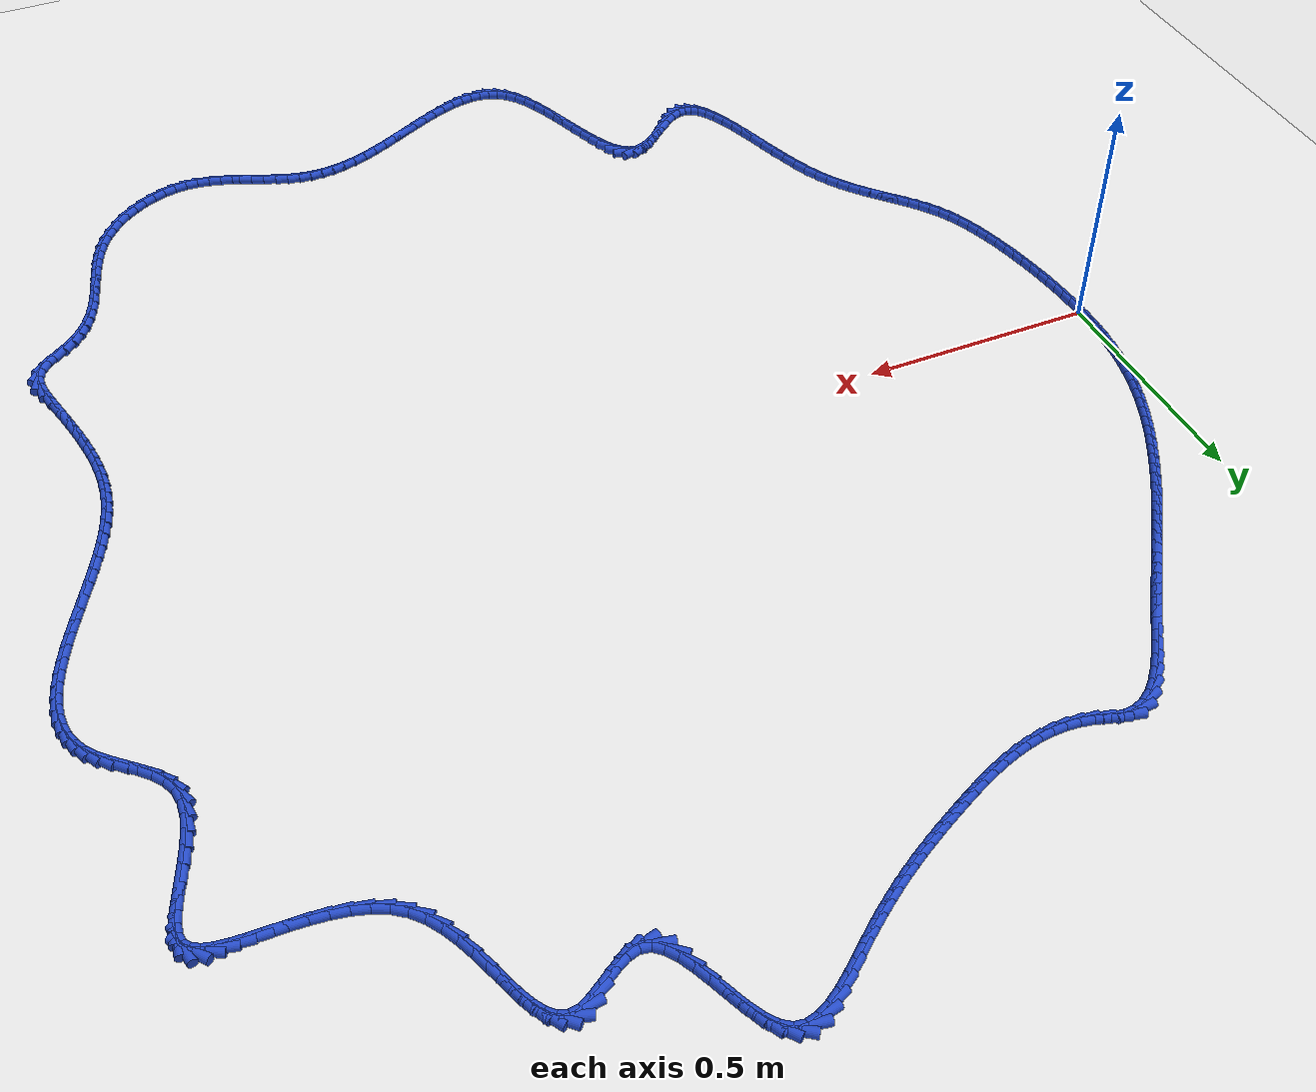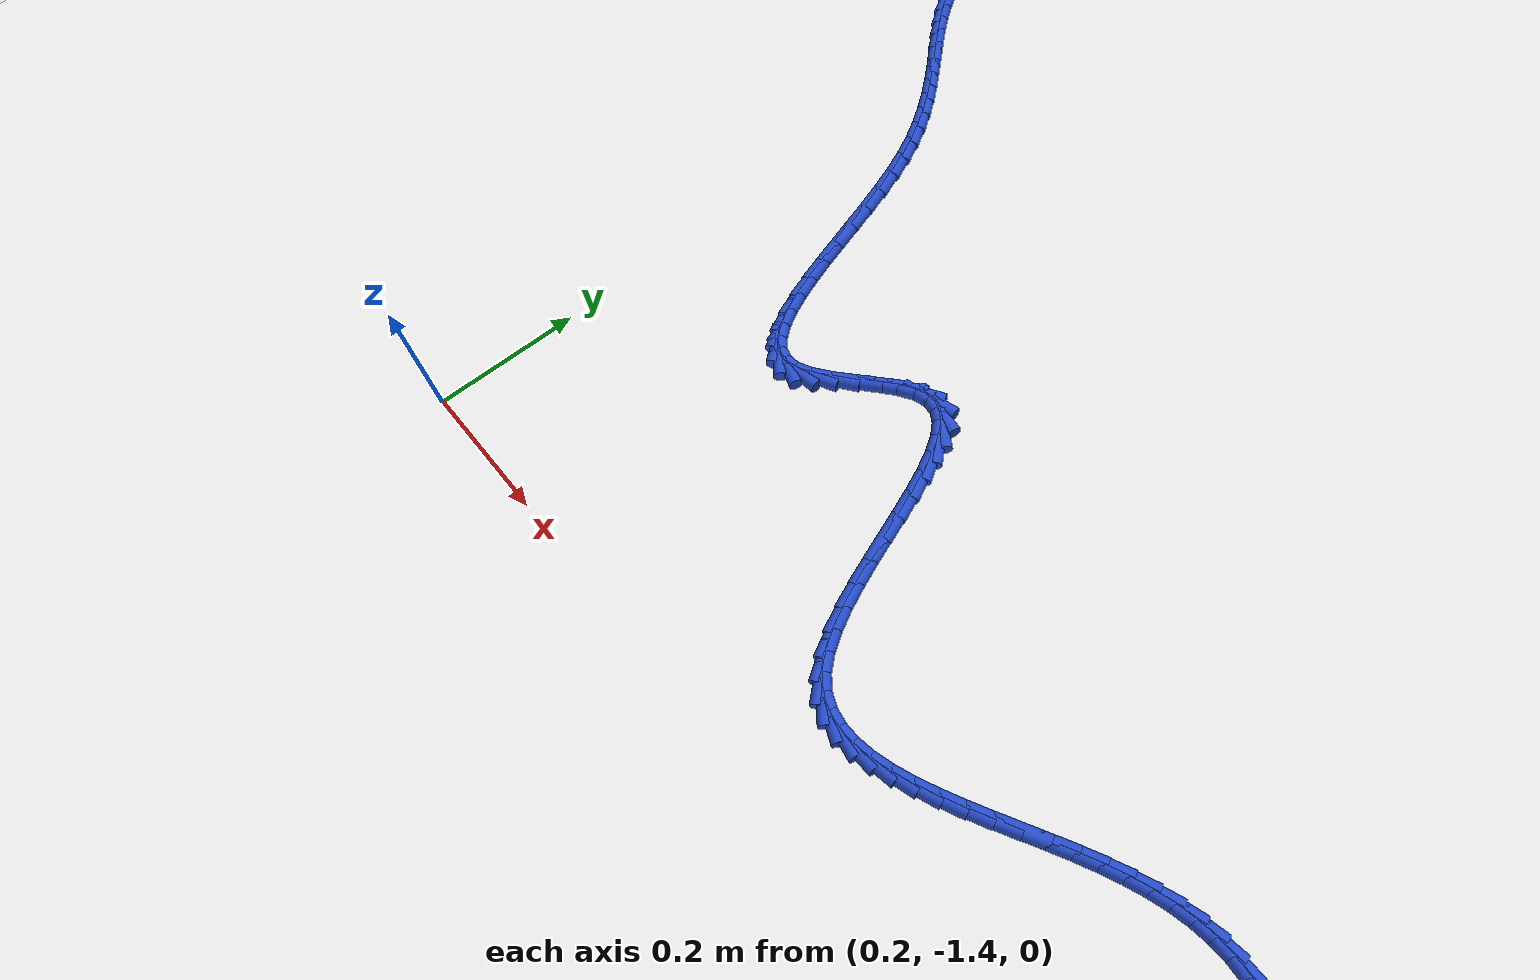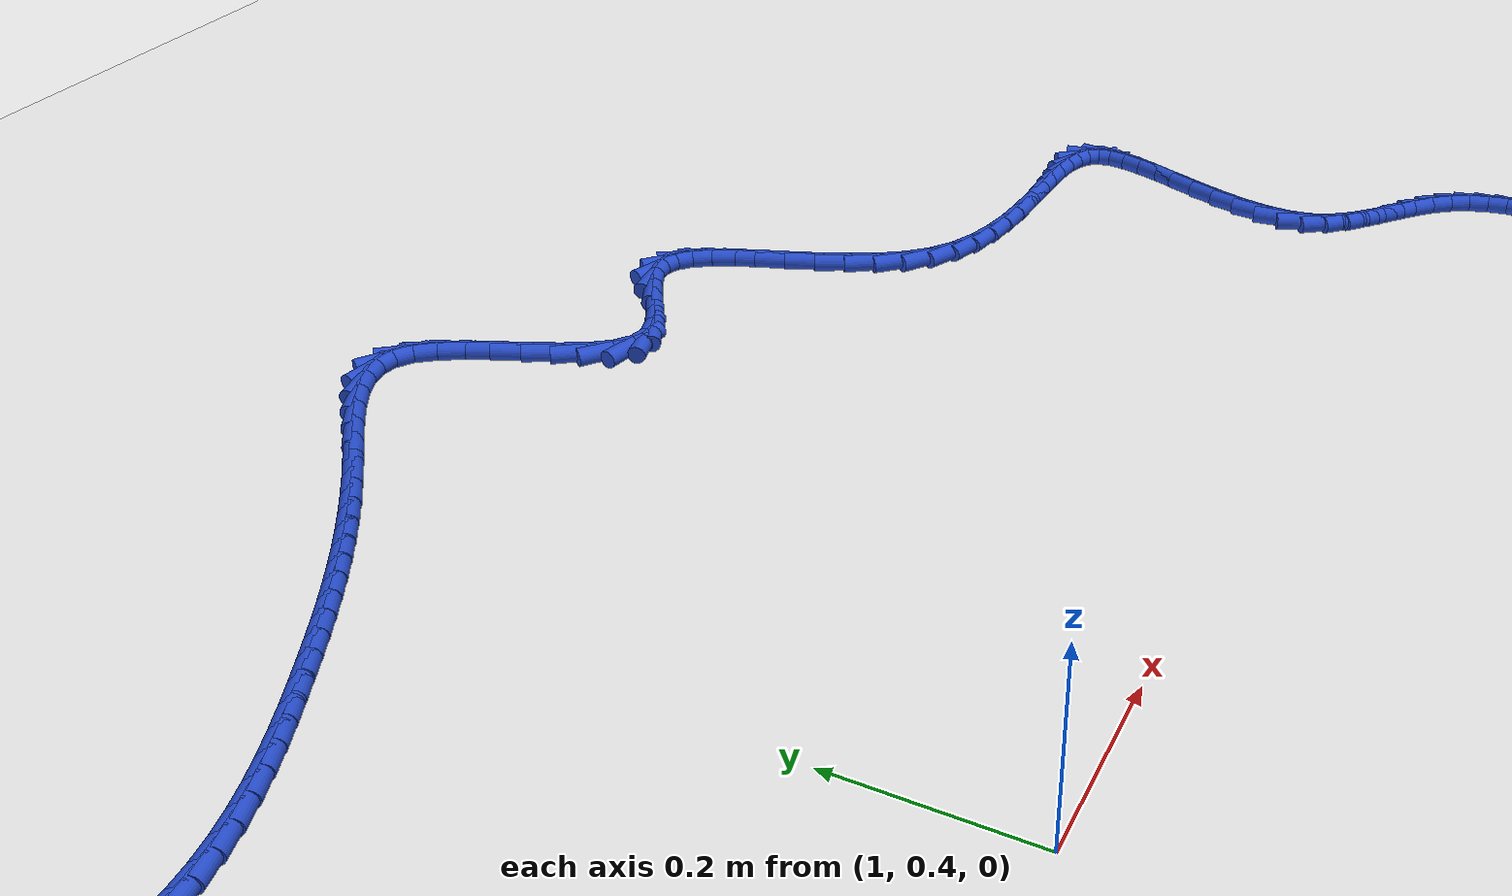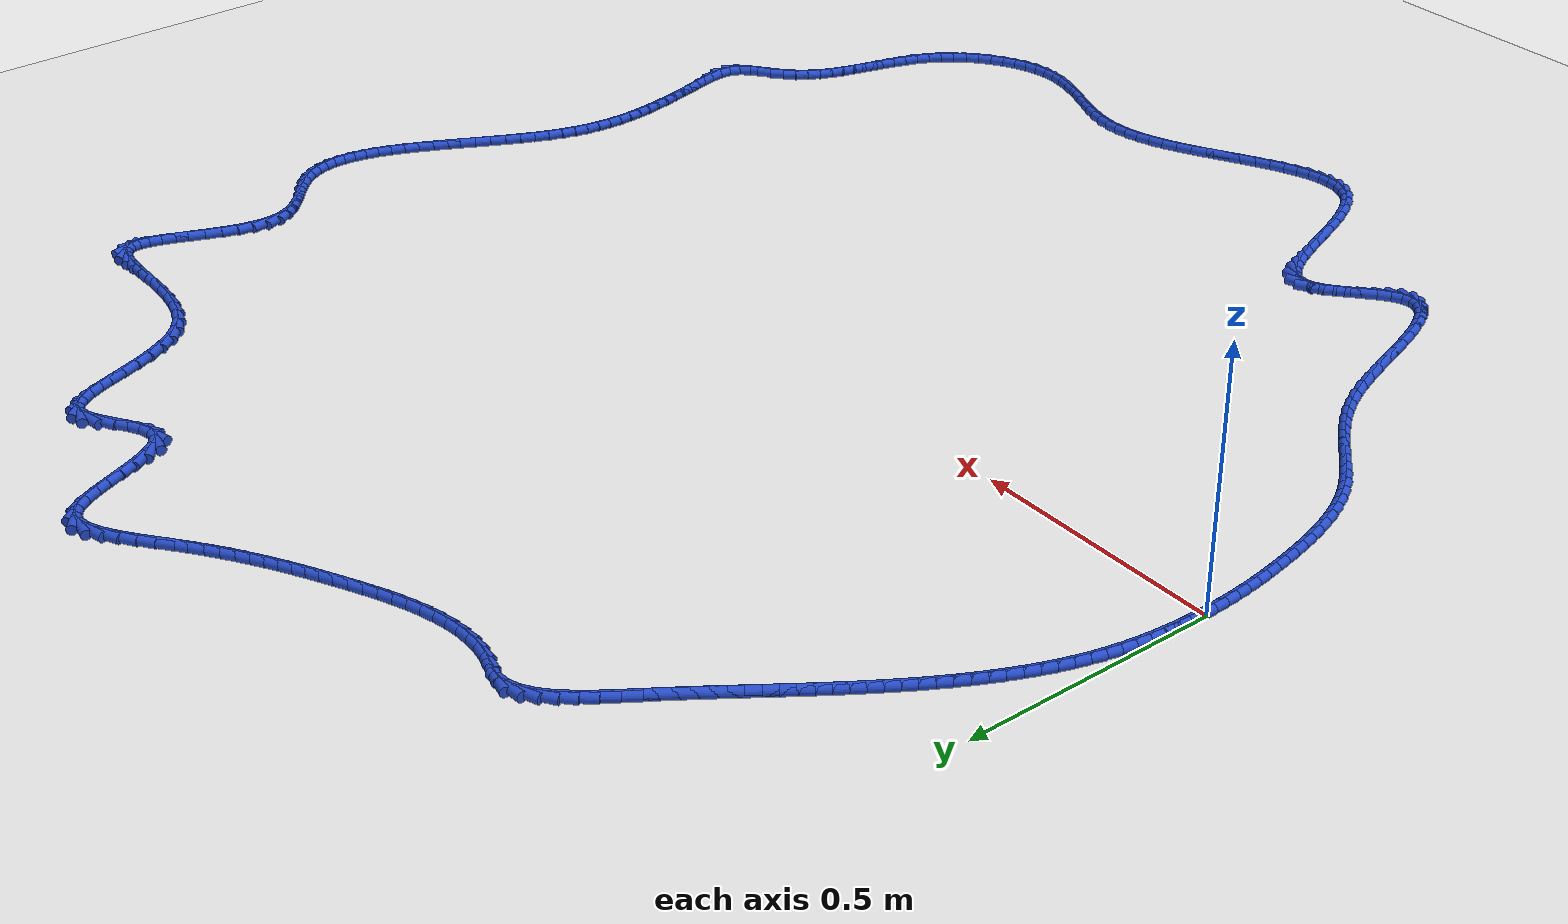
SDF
<sdf version="1.6">
 <world name="default">
  <light name="sun" type="directional">
   <pose>0 0 10 0 -0 0</pose>
   <diffuse>0.8 0.8 0.8 1</diffuse>
   <specular>0.2 0.2 0.2 1</specular>
   <attenuation>
    <range>1000</range>
    <constant>0.9</constant>
    <linear>0.01</linear>
    <quadratic>0.001</quadratic>
   </attenuation>
   <direction>-0.5 0.1 -0.9</direction>
  </light>
  <model name="ground_plane">
   <static>1</static>
   <link name="link">
    <collision name="collision">
     <geometry><plane><normal>0 0 1</normal><size>100 100</size></plane></geometry>
     <surface><friction><ode><mu>100</mu><mu2>50</mu2></ode></friction></surface>
    </collision>
    <visual name="visual">
     <cast_shadows>0</cast_shadows>
     <geometry><plane><normal>0 0 1</normal><size>100 100</size></plane></geometry>
     <material>
      <script><uri>file://media/materials/scripts/gazebo.material</uri><name>Gazebo/WhiteGlow</name></script>
     </material>
    </visual>
   </link>
  </model>
  <gravity>0 0 -9.8</gravity>
  <magnetic_field>6e-06 2.3e-05 -4.2e-05</magnetic_field>
  <atmosphere type="adiabatic"/>
  <physics name="default_physics" default="0" type="ode">
   <max_step_size>0.001</max_step_size>
   <real_time_factor>1</real_time_factor>
   <real_time_update_rate>1000</real_time_update_rate>
  </physics>
  <scene><ambient>0.4 0.4 0.4 1</ambient><background>0.7 0.7 0.7 1</background><shadows>1</shadows></scene>
  <spherical_coordinates>
   <surface_model>EARTH_WGS84</surface_model>
   <latitude_deg>0</latitude_deg>
   <longitude_deg>0</longitude_deg>
   <elevation>0</elevation>
   <heading_deg>0</heading_deg>
  </spherical_coordinates>
  <model name="line">
   <link name="link_0">
    <pose>1.3010426069826053e-17 2.0816681711721685e-17 0.01 0 1.57 -1.5697173017032293</pose>
    <collision name="collision">
     <geometry><cylinder><radius>0.01</radius><length>0.08</length></cylinder></geometry>
    </collision>
    <visual name="visual">
     <material>
      <script><name>Gazebo/Blue</name><uri>file://media/materials/scripts/gazebo.material</uri></script>
     </material>
     <geometry><cylinder><radius>0.01</radius><length>0.08</length></cylinder></geometry>
    </visual>
   </link>
   <link name="link_1">
    <pose>-2.9200421300071996e-05 0.027061845172039942 0.01 0 1.57 1.5444949600716549</pose>
    <collision name="collision">
     <geometry><cylinder><radius>0.01</radius><length>0.08</length></cylinder></geometry>
    </collision>
    <visual name="visual">
     <material>
      <script><name>Gazebo/Blue</name><uri>file://media/materials/scripts/gazebo.material</uri></script>
     </material>
     <geometry><cylinder><radius>0.01</radius><length>0.08</length></cylinder></geometry>
    </visual>
   </link>
   <link name="link_2">
    <pose>0.0006842096569551237 0.054180039251902304 0.01 0 1.57 1.5151995954347877</pose>
    <collision name="collision">
     <geometry><cylinder><radius>0.01</radius><length>0.08</length></cylinder></geometry>
    </collision>
    <visual name="visual">
     <material>
      <script><name>Gazebo/Blue</name><uri>file://media/materials/scripts/gazebo.material</uri></script>
     </material>
     <geometry><cylinder><radius>0.01</radius><length>0.08</length></cylinder></geometry>
    </visual>
   </link>
   <link name="link_3">
    <pose>0.002194301996070999 0.08131357902605951 0.01 0 1.57 1.4839247480656252</pose>
    <collision name="collision">
     <geometry><cylinder><radius>0.01</radius><length>0.08</length></cylinder></geometry>
    </collision>
    <visual name="visual">
     <material>
      <script><name>Gazebo/Blue</name><uri>file://media/materials/scripts/gazebo.material</uri></script>
     </material>
     <geometry><cylinder><radius>0.01</radius><length>0.08</length></cylinder></geometry>
    </visual>
   </link>
   <link name="link_4">
    <pose>0.004555148357352962 0.10842146128098404 0.01 0 1.57 1.4506119062643106</pose>
    <collision name="collision">
     <geometry><cylinder><radius>0.01</radius><length>0.08</length></cylinder></geometry>
    </collision>
    <visual name="visual">
     <material>
      <script><name>Gazebo/Blue</name><uri>file://media/materials/scripts/gazebo.material</uri></script>
     </material>
     <geometry><cylinder><radius>0.01</radius><length>0.08</length></cylinder></geometry>
    </visual>
   </link>
   <link name="link_5">
    <pose>0.007820820502106415 0.13546268280314816 0.01 0 1.57 1.4152124454950412</pose>
    <collision name="collision">
     <geometry><cylinder><radius>0.01</radius><length>0.08</length></cylinder></geometry>
    </collision>
    <visual name="visual">
     <material>
      <script><name>Gazebo/Blue</name><uri>file://media/materials/scripts/gazebo.material</uri></script>
     </material>
     <geometry><cylinder><radius>0.01</radius><length>0.08</length></cylinder></geometry>
    </visual>
   </link>
   <link name="link_6">
    <pose>0.012045390191636758 0.1623962403790244 0.01 0 1.57 1.377692109483791</pose>
    <collision name="collision">
     <geometry><cylinder><radius>0.01</radius><length>0.08</length></cylinder></geometry>
    </collision>
    <visual name="visual">
     <material>
      <script><name>Gazebo/Blue</name><uri>file://media/materials/scripts/gazebo.material</uri></script>
     </material>
     <geometry><cylinder><radius>0.01</radius><length>0.08</length></cylinder></geometry>
    </visual>
   </link>
   <link name="link_7">
    <pose>0.0172829291872494 0.18918113079508506 0.01 0 1.57 1.3380360453744053</pose>
    <collision name="collision">
     <geometry><cylinder><radius>0.01</radius><length>0.08</length></cylinder></geometry>
    </collision>
    <visual name="visual">
     <material>
      <script><name>Gazebo/Blue</name><uri>file://media/materials/scripts/gazebo.material</uri></script>
     </material>
     <geometry><cylinder><radius>0.01</radius><length>0.08</length></cylinder></geometry>
    </visual>
   </link>
   <link name="link_8">
    <pose>0.023587508601963982 0.21577635093613604 0.01 0 1.57 1.297177161098241</pose>
    <collision name="collision">
     <geometry><cylinder><radius>0.01</radius><length>0.08</length></cylinder></geometry>
    </collision>
    <visual name="visual">
     <material>
      <script><name>Gazebo/Blue</name><uri>file://media/materials/scripts/gazebo.material</uri></script>
     </material>
     <geometry><cylinder><radius>0.01</radius><length>0.08</length></cylinder></geometry>
    </visual>
   </link>
   <link name="link_9">
    <pose>0.030988013248767855 0.2421447179992894 0.01 0 1.57 1.2584734507983595</pose>
    <collision name="collision">
     <geometry><cylinder><radius>0.01</radius><length>0.08</length></cylinder></geometry>
    </collision>
    <visual name="visual">
     <material>
      <script><name>Gazebo/Blue</name><uri>file://media/materials/scripts/gazebo.material</uri></script>
     </material>
     <geometry><cylinder><radius>0.01</radius><length>0.08</length></cylinder></geometry>
    </visual>
   </link>
   <link name="link_10">
    <pose>0.039421361722653536 0.26826299881593973 0.01 0 1.57 1.2226131388580286</pose>
    <collision name="collision">
     <geometry><cylinder><radius>0.01</radius><length>0.08</length></cylinder></geometry>
    </collision>
    <visual name="visual">
     <material>
      <script><name>Gazebo/Blue</name><uri>file://media/materials/scripts/gazebo.material</uri></script>
     </material>
     <geometry><cylinder><radius>0.01</radius><length>0.08</length></cylinder></geometry>
    </visual>
   </link>
   <link name="link_11">
    <pose>0.04880348759329643 0.2941111432713786 0.01 0 1.57 1.189492367818633</pose>
    <collision name="collision">
     <geometry><cylinder><radius>0.01</radius><length>0.08</length></cylinder></geometry>
    </collision>
    <visual name="visual">
     <material>
      <script><name>Gazebo/Blue</name><uri>file://media/materials/scripts/gazebo.material</uri></script>
     </material>
     <geometry><cylinder><radius>0.01</radius><length>0.08</length></cylinder></geometry>
    </visual>
   </link>
   <link name="link_12">
    <pose>0.05905032443037188 0.31966910125089765 0.01 0 1.57 1.1589976364144043</pose>
    <collision name="collision">
     <geometry><cylinder><radius>0.01</radius><length>0.08</length></cylinder></geometry>
    </collision>
    <visual name="visual">
     <material>
      <script><name>Gazebo/Blue</name><uri>file://media/materials/scripts/gazebo.material</uri></script>
     </material>
     <geometry><cylinder><radius>0.01</radius><length>0.08</length></cylinder></geometry>
    </visual>
   </link>
   <link name="link_13">
    <pose>0.07007780580355527 0.34491682263978823 0.01 0 1.57 1.1310126287522888</pose>
    <collision name="collision">
     <geometry><cylinder><radius>0.01</radius><length>0.08</length></cylinder></geometry>
    </collision>
    <visual name="visual">
     <material>
      <script><name>Gazebo/Blue</name><uri>file://media/materials/scripts/gazebo.material</uri></script>
     </material>
     <geometry><cylinder><radius>0.01</radius><length>0.08</length></cylinder></geometry>
    </visual>
   </link>
   <link name="link_14">
    <pose>0.081801865282522 0.3698342573233421 0.01 0 1.57 1.105423599570831</pose>
    <collision name="collision">
     <geometry><cylinder><radius>0.01</radius><length>0.08</length></cylinder></geometry>
    </collision>
    <visual name="visual">
     <material>
      <script><name>Gazebo/Blue</name><uri>file://media/materials/scripts/gazebo.material</uri></script>
     </material>
     <geometry><cylinder><radius>0.01</radius><length>0.08</length></cylinder></geometry>
    </visual>
   </link>
   <link name="link_15">
    <pose>0.0941384364369474 0.3944013551868507 0.01 0 1.57 1.0821235650894114</pose>
    <collision name="collision">
     <geometry><cylinder><radius>0.01</radius><length>0.08</length></cylinder></geometry>
    </collision>
    <visual name="visual">
     <material>
      <script><name>Gazebo/Blue</name><uri>file://media/materials/scripts/gazebo.material</uri></script>
     </material>
     <geometry><cylinder><radius>0.01</radius><length>0.08</length></cylinder></geometry>
    </visual>
   </link>
   <link name="link_16">
    <pose>0.10700345283650689 0.4185980661156056 0.01 0 1.57 1.061015569920367</pose>
    <collision name="collision">
     <geometry><cylinder><radius>0.01</radius><length>0.08</length></cylinder></geometry>
    </collision>
    <visual name="visual">
     <material>
      <script><name>Gazebo/Blue</name><uri>file://media/materials/scripts/gazebo.material</uri></script>
     </material>
     <geometry><cylinder><radius>0.01</radius><length>0.08</length></cylinder></geometry>
    </visual>
   </link>
   <link name="link_17">
    <pose>0.12031284805087583 0.4424043399948985 0.01 0 1.57 1.0420152957055933</pose>
    <collision name="collision">
     <geometry><cylinder><radius>0.01</radius><length>0.08</length></cylinder></geometry>
    </collision>
    <visual name="visual">
     <material>
      <script><name>Gazebo/Blue</name><uri>file://media/materials/scripts/gazebo.material</uri></script>
     </material>
     <geometry><cylinder><radius>0.01</radius><length>0.08</length></cylinder></geometry>
    </visual>
   </link>
   <link name="link_18">
    <pose>0.1339825556497296 0.4658001267100208 0.01 0 1.57 1.0250532614204548</pose>
    <collision name="collision">
     <geometry><cylinder><radius>0.01</radius><length>0.08</length></cylinder></geometry>
    </collision>
    <visual name="visual">
     <material>
      <script><name>Gazebo/Blue</name><uri>file://media/materials/scripts/gazebo.material</uri></script>
     </material>
     <geometry><cylinder><radius>0.01</radius><length>0.08</length></cylinder></geometry>
    </visual>
   </link>
   <link name="link_19">
    <pose>0.14792850920274353 0.488765376146264 0.01 0 1.57 1.0100768490725263</pose>
    <collision name="collision">
     <geometry><cylinder><radius>0.01</radius><length>0.08</length></cylinder></geometry>
    </collision>
    <visual name="visual">
     <material>
      <script><name>Gazebo/Blue</name><uri>file://media/materials/scripts/gazebo.material</uri></script>
     </material>
     <geometry><cylinder><radius>0.01</radius><length>0.08</length></cylinder></geometry>
    </visual>
   </link>
   <link name="link_20">
    <pose>0.1620666422795931 0.5112800381889199 0.01 0 1.57 0.9970488804408632</pose>
    <collision name="collision">
     <geometry><cylinder><radius>0.01</radius><length>0.08</length></cylinder></geometry>
    </collision>
    <visual name="visual">
     <material>
      <script><name>Gazebo/Blue</name><uri>file://media/materials/scripts/gazebo.material</uri></script>
     </material>
     <geometry><cylinder><radius>0.01</radius><length>0.08</length></cylinder></geometry>
    </visual>
   </link>
   <link name="link_21">
    <pose>0.17631340872781767 0.5333246985951458 0.01 0 1.57 0.9857089173041975</pose>
    <collision name="collision">
     <geometry><cylinder><radius>0.01</radius><length>0.08</length></cylinder></geometry>
    </collision>
    <visual name="visual">
     <material>
      <script><name>Gazebo/Blue</name><uri>file://media/materials/scripts/gazebo.material</uri></script>
     </material>
     <geometry><cylinder><radius>0.01</radius><length>0.08</length></cylinder></geometry>
    </visual>
   </link>
   <link name="link_22">
    <pose>0.19062581661681963 0.5549295075769992 0.01 0 1.57 0.9757428286752328</pose>
    <collision name="collision">
     <geometry><cylinder><radius>0.01</radius><length>0.08</length></cylinder></geometry>
    </collision>
    <visual name="visual">
     <material>
      <script><name>Gazebo/Blue</name><uri>file://media/materials/scripts/gazebo.material</uri></script>
     </material>
     <geometry><cylinder><radius>0.01</radius><length>0.08</length></cylinder></geometry>
    </visual>
   </link>
   <link name="link_23">
    <pose>0.2050297864740089 0.5762088385977815 0.01 0 1.57 0.9672819725678445</pose>
    <collision name="collision">
     <geometry><cylinder><radius>0.01</radius><length>0.08</length></cylinder></geometry>
    </collision>
    <visual name="visual">
     <material>
      <script><name>Gazebo/Blue</name><uri>file://media/materials/scripts/gazebo.material</uri></script>
     </material>
     <geometry><cylinder><radius>0.01</radius><length>0.08</length></cylinder></geometry>
    </visual>
   </link>
   <link name="link_24">
    <pose>0.21955793547863278 0.5972852496175668 0.01 0 1.57 0.9604632881481213</pose>
    <collision name="collision">
     <geometry><cylinder><radius>0.01</radius><length>0.08</length></cylinder></geometry>
    </collision>
    <visual name="visual">
     <material>
      <script><name>Gazebo/Blue</name><uri>file://media/materials/scripts/gazebo.material</uri></script>
     </material>
     <geometry><cylinder><radius>0.01</radius><length>0.08</length></cylinder></geometry>
    </visual>
   </link>
   <link name="link_25">
    <pose>0.2342428808099382 0.6182812985964294 0.01 0 1.57 0.9553776776413522</pose>
    <collision name="collision">
     <geometry><cylinder><radius>0.01</radius><length>0.08</length></cylinder></geometry>
    </collision>
    <visual name="visual">
     <material>
      <script><name>Gazebo/Blue</name><uri>file://media/materials/scripts/gazebo.material</uri></script>
     </material>
     <geometry><cylinder><radius>0.01</radius><length>0.08</length></cylinder></geometry>
    </visual>
   </link>
   <link name="link_26">
    <pose>0.24911723964717222 0.6393195434944434 0.01 0 1.57 0.9520665482746776</pose>
    <collision name="collision">
     <geometry><cylinder><radius>0.01</radius><length>0.08</length></cylinder></geometry>
    </collision>
    <visual name="visual">
     <material>
      <script><name>Gazebo/Blue</name><uri>file://media/materials/scripts/gazebo.material</uri></script>
     </material>
     <geometry><cylinder><radius>0.01</radius><length>0.08</length></cylinder></geometry>
    </visual>
   </link>
   <link name="link_27">
    <pose>0.264213629169582 0.6605225422716826 0.01 0 1.57 0.9505217134233779</pose>
    <collision name="collision">
     <geometry><cylinder><radius>0.01</radius><length>0.08</length></cylinder></geometry>
    </collision>
    <visual name="visual">
     <material>
      <script><name>Gazebo/Blue</name><uri>file://media/materials/scripts/gazebo.material</uri></script>
     </material>
     <geometry><cylinder><radius>0.01</radius><length>0.08</length></cylinder></geometry>
    </visual>
   </link>
   <link name="link_28">
    <pose>0.2795646665564146 0.6820128528882213 0.01 0 1.57 0.9506884653868233</pose>
    <collision name="collision">
     <geometry><cylinder><radius>0.01</radius><length>0.08</length></cylinder></geometry>
    </collision>
    <visual name="visual">
     <material>
      <script><name>Gazebo/Blue</name><uri>file://media/materials/scripts/gazebo.material</uri></script>
     </material>
     <geometry><cylinder><radius>0.01</radius><length>0.08</length></cylinder></geometry>
    </visual>
   </link>
   <link name="link_29">
    <pose>0.29520296898691717 0.7039130333041339 0.01 0 1.57 0.9524712953232691</pose>
    <collision name="collision">
     <geometry><cylinder><radius>0.01</radius><length>0.08</length></cylinder></geometry>
    </collision>
    <visual name="visual">
     <material>
      <script><name>Gazebo/Blue</name><uri>file://media/materials/scripts/gazebo.material</uri></script>
     </material>
     <geometry><cylinder><radius>0.01</radius><length>0.08</length></cylinder></geometry>
    </visual>
   </link>
   <link name="link_30">
    <pose>0.3111611536403367 0.7263456414794943 0.01 0 1.57 0.9557415091581019</pose>
    <collision name="collision">
     <geometry><cylinder><radius>0.01</radius><length>0.08</length></cylinder></geometry>
    </collision>
    <visual name="visual">
     <material>
      <script><name>Gazebo/Blue</name><uri>file://media/materials/scripts/gazebo.material</uri></script>
     </material>
     <geometry><cylinder><radius>0.01</radius><length>0.08</length></cylinder></geometry>
    </visual>
   </link>
   <link name="link_31">
    <pose>0.3274718376959202 0.7494332353743766 0.01 0 1.57 0.960345891499181</pose>
    <collision name="collision">
     <geometry><cylinder><radius>0.01</radius><length>0.08</length></cylinder></geometry>
    </collision>
    <visual name="visual">
     <material>
      <script><name>Gazebo/Blue</name><uri>file://media/materials/scripts/gazebo.material</uri></script>
     </material>
     <geometry><cylinder><radius>0.01</radius><length>0.08</length></cylinder></geometry>
    </visual>
   </link>
   <link name="link_32">
    <pose>0.344167638332915 0.7732983729488551 0.01 0 1.57 0.9661155952133936</pose>
    <collision name="collision">
     <geometry><cylinder><radius>0.01</radius><length>0.08</length></cylinder></geometry>
    </collision>
    <visual name="visual">
     <material>
      <script><name>Gazebo/Blue</name><uri>file://media/materials/scripts/gazebo.material</uri></script>
     </material>
     <geometry><cylinder><radius>0.01</radius><length>0.08</length></cylinder></geometry>
    </visual>
   </link>
   <link name="link_33">
    <pose>0.36128117273056803 0.7980636121630038 0.01 0 1.57 0.9728134124557227</pose>
    <collision name="collision">
     <geometry><cylinder><radius>0.01</radius><length>0.08</length></cylinder></geometry>
    </collision>
    <visual name="visual">
     <material>
      <script><name>Gazebo/Blue</name><uri>file://media/materials/scripts/gazebo.material</uri></script>
     </material>
     <geometry><cylinder><radius>0.01</radius><length>0.08</length></cylinder></geometry>
    </visual>
   </link>
   <link name="link_34">
    <pose>0.3788452236043237 0.8238483653737788 0.01 0 1.57 0.9730356652216618</pose>
    <collision name="collision">
     <geometry><cylinder><radius>0.01</radius><length>0.08</length></cylinder></geometry>
    </collision>
    <visual name="visual">
     <material>
      <script><name>Gazebo/Blue</name><uri>file://media/materials/scripts/gazebo.material</uri></script>
     </material>
     <geometry><cylinder><radius>0.01</radius><length>0.08</length></cylinder></geometry>
    </visual>
   </link>
   <link name="link_35">
    <pose>0.3969129321458374 0.8503851828061529 0.01 0 1.57 0.9530143231418904</pose>
    <collision name="collision">
     <geometry><cylinder><radius>0.01</radius><length>0.08</length></cylinder></geometry>
    </collision>
    <visual name="visual">
     <material>
      <script><name>Gazebo/Blue</name><uri>file://media/materials/scripts/gazebo.material</uri></script>
     </material>
     <geometry><cylinder><radius>0.01</radius><length>0.08</length></cylinder></geometry>
    </visual>
   </link>
   <link name="link_36">
    <pose>0.41557715671589757 0.8766518888122864 0.01 0 1.57 0.9097168254434055</pose>
    <collision name="collision">
     <geometry><cylinder><radius>0.01</radius><length>0.08</length></cylinder></geometry>
    </collision>
    <visual name="visual">
     <material>
      <script><name>Gazebo/Blue</name><uri>file://media/materials/scripts/gazebo.material</uri></script>
     </material>
     <geometry><cylinder><radius>0.01</radius><length>0.08</length></cylinder></geometry>
    </visual>
   </link>
   <link name="link_37">
    <pose>0.43493534386232124 0.9015391206780022 0.01 0 1.57 0.8382022605168087</pose>
    <collision name="collision">
     <geometry><cylinder><radius>0.01</radius><length>0.08</length></cylinder></geometry>
    </collision>
    <visual name="visual">
     <material>
      <script><name>Gazebo/Blue</name><uri>file://media/materials/scripts/gazebo.material</uri></script>
     </material>
     <geometry><cylinder><radius>0.01</radius><length>0.08</length></cylinder></geometry>
    </visual>
   </link>
   <link name="link_38">
    <pose>0.45508494013292605 0.9239375156891247 0.01 0 1.57 0.7292741217284323</pose>
    <collision name="collision">
     <geometry><cylinder><radius>0.01</radius><length>0.08</length></cylinder></geometry>
    </collision>
    <visual name="visual">
     <material>
      <script><name>Gazebo/Blue</name><uri>file://media/materials/scripts/gazebo.material</uri></script>
     </material>
     <geometry><cylinder><radius>0.01</radius><length>0.08</length></cylinder></geometry>
    </visual>
   </link>
   <link name="link_39">
    <pose>0.47612339207552895 0.9427377111314772 0.01 0 1.57 0.5692098055685585</pose>
    <collision name="collision">
     <geometry><cylinder><radius>0.01</radius><length>0.08</length></cylinder></geometry>
    </collision>
    <visual name="visual">
     <material>
      <script><name>Gazebo/Blue</name><uri>file://media/materials/scripts/gazebo.material</uri></script>
     </material>
     <geometry><cylinder><radius>0.01</radius><length>0.08</length></cylinder></geometry>
    </visual>
   </link>
   <link name="link_40">
    <pose>0.49814814623794745 0.9568303442908832 0.01 0 1.57 0.34389377227890133</pose>
    <collision name="collision">
     <geometry><cylinder><radius>0.01</radius><length>0.08</length></cylinder></geometry>
    </collision>
    <visual name="visual">
     <material>
      <script><name>Gazebo/Blue</name><uri>file://media/materials/scripts/gazebo.material</uri></script>
     </material>
     <geometry><cylinder><radius>0.01</radius><length>0.08</length></cylinder></geometry>
    </visual>
   </link>
   <link name="link_41">
    <pose>0.5212566491679989 0.9651060524531663 0.01 0 1.57 0.05549820853235824</pose>
    <collision name="collision">
     <geometry><cylinder><radius>0.01</radius><length>0.08</length></cylinder></geometry>
    </collision>
    <visual name="visual">
     <material>
      <script><name>Gazebo/Blue</name><uri>file://media/materials/scripts/gazebo.material</uri></script>
     </material>
     <geometry><cylinder><radius>0.01</radius><length>0.08</length></cylinder></geometry>
    </visual>
   </link>
   <link name="link_42">
    <pose>0.5455463474135003 0.96645547290415 0.01 0 1.57 -0.2350668429261476</pose>
    <collision name="collision">
     <geometry><cylinder><radius>0.01</radius><length>0.08</length></cylinder></geometry>
    </collision>
    <visual name="visual">
     <material>
      <script><name>Gazebo/Blue</name><uri>file://media/materials/scripts/gazebo.material</uri></script>
     </material>
     <geometry><cylinder><radius>0.01</radius><length>0.08</length></cylinder></geometry>
    </visual>
   </link>
   <link name="link_43">
    <pose>0.5710711136635586 0.9603424348504531 0.01 0 1.57 -0.30181040248448376</pose>
    <collision name="collision">
     <geometry><cylinder><radius>0.01</radius><length>0.08</length></cylinder></geometry>
    </collision>
    <visual name="visual">
     <material>
      <script><name>Gazebo/Blue</name><uri>file://media/materials/scripts/gazebo.material</uri></script>
     </material>
     <geometry><cylinder><radius>0.01</radius><length>0.08</length></cylinder></geometry>
    </visual>
   </link>
   <link name="link_44">
    <pose>0.5974346698493049 0.9521349061430052 0.01 0 1.57 -0.19079171505916978</pose>
    <collision name="collision">
     <geometry><cylinder><radius>0.01</radius><length>0.08</length></cylinder></geometry>
    </collision>
    <visual name="visual">
     <material>
      <script><name>Gazebo/Blue</name><uri>file://media/materials/scripts/gazebo.material</uri></script>
     </material>
     <geometry><cylinder><radius>0.01</radius><length>0.08</length></cylinder></geometry>
    </visual>
   </link>
   <link name="link_45">
    <pose>0.6242030603973368 0.9469648334704381 0.01 0 1.57 -0.07663513551249</pose>
    <collision name="collision">
     <geometry><cylinder><radius>0.01</radius><length>0.08</length></cylinder></geometry>
    </collision>
    <visual name="visual">
     <material>
      <script><name>Gazebo/Blue</name><uri>file://media/materials/scripts/gazebo.material</uri></script>
     </material>
     <geometry><cylinder><radius>0.01</radius><length>0.08</length></cylinder></geometry>
    </visual>
   </link>
   <link name="link_46">
    <pose>0.6512533928669875 0.9448877598039425 0.01 0 1.57 0.026088019033160104</pose>
    <collision name="collision">
     <geometry><cylinder><radius>0.01</radius><length>0.08</length></cylinder></geometry>
    </collision>
    <visual name="visual">
     <material>
      <script><name>Gazebo/Blue</name><uri>file://media/materials/scripts/gazebo.material</uri></script>
     </material>
     <geometry><cylinder><radius>0.01</radius><length>0.08</length></cylinder></geometry>
    </visual>
   </link>
   <link name="link_47">
    <pose>0.6784849381984444 0.9455983380870778 0.01 0 1.57 0.11637568455757877</pose>
    <collision name="collision">
     <geometry><cylinder><radius>0.01</radius><length>0.08</length></cylinder></geometry>
    </collision>
    <visual name="visual">
     <material>
      <script><name>Gazebo/Blue</name><uri>file://media/materials/scripts/gazebo.material</uri></script>
     </material>
     <geometry><cylinder><radius>0.01</radius><length>0.08</length></cylinder></geometry>
    </visual>
   </link>
   <link name="link_48">
    <pose>0.7057969673318943 0.9487912212634037 0.01 0 1.57 0.1942750547246561</pose>
    <collision name="collision">
     <geometry><cylinder><radius>0.01</radius><length>0.08</length></cylinder></geometry>
    </collision>
    <visual name="visual">
     <material>
      <script><name>Gazebo/Blue</name><uri>file://media/materials/scripts/gazebo.material</uri></script>
     </material>
     <geometry><cylinder><radius>0.01</radius><length>0.08</length></cylinder></geometry>
    </visual>
   </link>
   <link name="link_49">
    <pose>0.7330887512075247 0.9541610622764796 0.01 0 1.57 0.2604615958813891</pose>
    <collision name="collision">
     <geometry><cylinder><radius>0.01</radius><length>0.08</length></cylinder></geometry>
    </collision>
    <visual name="visual">
     <material>
      <script><name>Gazebo/Blue</name><uri>file://media/materials/scripts/gazebo.material</uri></script>
     </material>
     <geometry><cylinder><radius>0.01</radius><length>0.08</length></cylinder></geometry>
    </visual>
   </link>
   <link name="link_50">
    <pose>0.7602595607655221 0.9614025140698645 0.01 0 1.57 0.31588413985902697</pose>
    <collision name="collision">
     <geometry><cylinder><radius>0.01</radius><length>0.08</length></cylinder></geometry>
    </collision>
    <visual name="visual">
     <material>
      <script><name>Gazebo/Blue</name><uri>file://media/materials/scripts/gazebo.material</uri></script>
     </material>
     <geometry><cylinder><radius>0.01</radius><length>0.08</length></cylinder></geometry>
    </visual>
   </link>
   <link name="link_51">
    <pose>0.7872086669460738 0.9702102295871187 0.01 0 1.57 0.3615214166022605</pose>
    <collision name="collision">
     <geometry><cylinder><radius>0.01</radius><length>0.08</length></cylinder></geometry>
    </collision>
    <visual name="visual">
     <material>
      <script><name>Gazebo/Blue</name><uri>file://media/materials/scripts/gazebo.material</uri></script>
     </material>
     <geometry><cylinder><radius>0.01</radius><length>0.08</length></cylinder></geometry>
    </visual>
   </link>
   <link name="link_52">
    <pose>0.8138353406893672 0.9802788617718015 0.01 0 1.57 0.398235335562047</pose>
    <collision name="collision">
     <geometry><cylinder><radius>0.01</radius><length>0.08</length></cylinder></geometry>
    </collision>
    <visual name="visual">
     <material>
      <script><name>Gazebo/Blue</name><uri>file://media/materials/scripts/gazebo.material</uri></script>
     </material>
     <geometry><cylinder><radius>0.01</radius><length>0.08</length></cylinder></geometry>
    </visual>
   </link>
   <link name="link_53">
    <pose>0.8400388529355893 0.9913030635674722 0.01 0 1.57 0.4266878115329776</pose>
    <collision name="collision">
     <geometry><cylinder><radius>0.01</radius><length>0.08</length></cylinder></geometry>
    </collision>
    <visual name="visual">
     <material>
      <script><name>Gazebo/Blue</name><uri>file://media/materials/scripts/gazebo.material</uri></script>
     </material>
     <geometry><cylinder><radius>0.01</radius><length>0.08</length></cylinder></geometry>
    </visual>
   </link>
   <link name="link_54">
    <pose>0.8657184746249265 1.0029774879176905 0.01 0 1.57 0.4472895999580837</pose>
    <collision name="collision">
     <geometry><cylinder><radius>0.01</radius><length>0.08</length></cylinder></geometry>
    </collision>
    <visual name="visual">
     <material>
      <script><name>Gazebo/Blue</name><uri>file://media/materials/scripts/gazebo.material</uri></script>
     </material>
     <geometry><cylinder><radius>0.01</radius><length>0.08</length></cylinder></geometry>
    </visual>
   </link>
   <link name="link_55">
    <pose>0.8907734766975667 1.0149967877660158 0.01 0 1.57 0.46021744132438674</pose>
    <collision name="collision">
     <geometry><cylinder><radius>0.01</radius><length>0.08</length></cylinder></geometry>
    </collision>
    <visual name="visual">
     <material>
      <script><name>Gazebo/Blue</name><uri>file://media/materials/scripts/gazebo.material</uri></script>
     </material>
     <geometry><cylinder><radius>0.01</radius><length>0.08</length></cylinder></geometry>
    </visual>
   </link>
   <link name="link_56">
    <pose>0.9151045815455 1.027058193689771 0.01 0 1.57 0.4692396125667356</pose>
    <collision name="collision">
     <geometry><cylinder><radius>0.01</radius><length>0.08</length></cylinder></geometry>
    </collision>
    <visual name="visual">
     <material>
      <script><name>Gazebo/Blue</name><uri>file://media/materials/scripts/gazebo.material</uri></script>
     </material>
     <geometry><cylinder><radius>0.01</radius><length>0.08</length></cylinder></geometry>
    </visual>
   </link>
   <link name="link_57">
    <pose>0.9387055104458468 1.0390240930187873 0.01 0 1.57 0.48050025321752987</pose>
    <collision name="collision">
     <geometry><cylinder><radius>0.01</radius><length>0.08</length></cylinder></geometry>
    </collision>
    <visual name="visual">
     <material>
      <script><name>Gazebo/Blue</name><uri>file://media/materials/scripts/gazebo.material</uri></script>
     </material>
     <geometry><cylinder><radius>0.01</radius><length>0.08</length></cylinder></geometry>
    </visual>
   </link>
   <link name="link_58">
    <pose>0.9617176390641111 1.0510190925626777 0.01 0 1.57 0.4944465477223395</pose>
    <collision name="collision">
     <geometry><cylinder><radius>0.01</radius><length>0.08</length></cylinder></geometry>
    </collision>
    <visual name="visual">
     <material>
      <script><name>Gazebo/Blue</name><uri>file://media/materials/scripts/gazebo.material</uri></script>
     </material>
     <geometry><cylinder><radius>0.01</radius><length>0.08</length></cylinder></geometry>
    </visual>
   </link>
   <link name="link_59">
    <pose>0.9842954633300945 1.0631910994129934 0.01 0 1.57 0.5108307671526923</pose>
    <collision name="collision">
     <geometry><cylinder><radius>0.01</radius><length>0.08</length></cylinder></geometry>
    </collision>
    <visual name="visual">
     <material>
      <script><name>Gazebo/Blue</name><uri>file://media/materials/scripts/gazebo.material</uri></script>
     </material>
     <geometry><cylinder><radius>0.01</radius><length>0.08</length></cylinder></geometry>
    </visual>
   </link>
   <link name="link_60">
    <pose>1.0065934791735986 1.075688020661285 0.01 0 1.57 0.5292737658786579</pose>
    <collision name="collision">
     <geometry><cylinder><radius>0.01</radius><length>0.08</length></cylinder></geometry>
    </collision>
    <visual name="visual">
     <material>
      <script><name>Gazebo/Blue</name><uri>file://media/materials/scripts/gazebo.material</uri></script>
     </material>
     <geometry><cylinder><radius>0.01</radius><length>0.08</length></cylinder></geometry>
    </visual>
   </link>
   <link name="link_61">
    <pose>1.028766182524426 1.0886577633991046 0.01 0 1.57 0.5492919035547316</pose>
    <collision name="collision">
     <geometry><cylinder><radius>0.01</radius><length>0.08</length></cylinder></geometry>
    </collision>
    <visual name="visual">
     <material>
      <script><name>Gazebo/Blue</name><uri>file://media/materials/scripts/gazebo.material</uri></script>
     </material>
     <geometry><cylinder><radius>0.01</radius><length>0.08</length></cylinder></geometry>
    </visual>
   </link>
   <link name="link_62">
    <pose>1.0509680693123775 1.1022482347180025 0.01 0 1.57 0.5703375533128149</pose>
    <collision name="collision">
     <geometry><cylinder><radius>0.01</radius><length>0.08</length></cylinder></geometry>
    </collision>
    <visual name="visual">
     <material>
      <script><name>Gazebo/Blue</name><uri>file://media/materials/scripts/gazebo.material</uri></script>
     </material>
     <geometry><cylinder><radius>0.01</radius><length>0.08</length></cylinder></geometry>
    </visual>
   </link>
   <link name="link_63">
    <pose>1.0733536354672548 1.1166073417095295 0.01 0 1.57 0.5918463514609686</pose>
    <collision name="collision">
     <geometry><cylinder><radius>0.01</radius><length>0.08</length></cylinder></geometry>
    </collision>
    <visual name="visual">
     <material>
      <script><name>Gazebo/Blue</name><uri>file://media/materials/scripts/gazebo.material</uri></script>
     </material>
     <geometry><cylinder><radius>0.01</radius><length>0.08</length></cylinder></geometry>
    </visual>
   </link>
   <link name="link_64">
    <pose>1.0960773769188605 1.131882991465238 0.01 0 1.57 0.6132829364597052</pose>
    <collision name="collision">
     <geometry><cylinder><radius>0.01</radius><length>0.08</length></cylinder></geometry>
    </collision>
    <visual name="visual">
     <material>
      <script><name>Gazebo/Blue</name><uri>file://media/materials/scripts/gazebo.material</uri></script>
     </material>
     <geometry><cylinder><radius>0.01</radius><length>0.08</length></cylinder></geometry>
    </visual>
   </link>
   <link name="link_65">
    <pose>1.1192937895969954 1.148223091076678 0.01 0 1.57 0.6341779198744755</pose>
    <collision name="collision">
     <geometry><cylinder><radius>0.01</radius><length>0.08</length></cylinder></geometry>
    </collision>
    <visual name="visual">
     <material>
      <script><name>Gazebo/Blue</name><uri>file://media/materials/scripts/gazebo.material</uri></script>
     </material>
     <geometry><cylinder><radius>0.01</radius><length>0.08</length></cylinder></geometry>
    </visual>
   </link>
   <link name="link_66">
    <pose>1.1431573694314616 1.165775547635401 0.01 0 1.57 0.6541516896999916</pose>
    <collision name="collision">
     <geometry><cylinder><radius>0.01</radius><length>0.08</length></cylinder></geometry>
    </collision>
    <visual name="visual">
     <material>
      <script><name>Gazebo/Blue</name><uri>file://media/materials/scripts/gazebo.material</uri></script>
     </material>
     <geometry><cylinder><radius>0.01</radius><length>0.08</length></cylinder></geometry>
    </visual>
   </link>
   <link name="link_67">
    <pose>1.1678226123520612 1.184688268232958 0.01 0 1.57 0.6699337207095273</pose>
    <collision name="collision">
     <geometry><cylinder><radius>0.01</radius><length>0.08</length></cylinder></geometry>
    </collision>
    <visual name="visual">
     <material>
      <script><name>Gazebo/Blue</name><uri>file://media/materials/scripts/gazebo.material</uri></script>
     </material>
     <geometry><cylinder><radius>0.01</radius><length>0.08</length></cylinder></geometry>
    </visual>
   </link>
   <link name="link_68">
    <pose>1.193374565082674 1.2049291530411803 0.01 0 1.57 0.6634497295644504</pose>
    <collision name="collision">
     <geometry><cylinder><radius>0.01</radius><length>0.08</length></cylinder></geometry>
    </collision>
    <visual name="visual">
     <material>
      <script><name>Gazebo/Blue</name><uri>file://media/materials/scripts/gazebo.material</uri></script>
     </material>
     <geometry><cylinder><radius>0.01</radius><length>0.08</length></cylinder></geometry>
    </visual>
   </link>
   <link name="link_69">
    <pose>1.2194537226837256 1.2253138590271848 0.01 0 1.57 0.6270090021061866</pose>
    <collision name="collision">
     <geometry><cylinder><radius>0.01</radius><length>0.08</length></cylinder></geometry>
    </collision>
    <visual name="visual">
     <material>
      <script><name>Gazebo/Blue</name><uri>file://media/materials/scripts/gazebo.material</uri></script>
     </material>
     <geometry><cylinder><radius>0.01</radius><length>0.08</length></cylinder></geometry>
    </visual>
   </link>
   <link name="link_70">
    <pose>1.2455253665182062 1.2442039029335945 0.01 0 1.57 0.5529510030765529</pose>
    <collision name="collision">
     <geometry><cylinder><radius>0.01</radius><length>0.08</length></cylinder></geometry>
    </collision>
    <visual name="visual">
     <material>
      <script><name>Gazebo/Blue</name><uri>file://media/materials/scripts/gazebo.material</uri></script>
     </material>
     <geometry><cylinder><radius>0.01</radius><length>0.08</length></cylinder></geometry>
    </visual>
   </link>
   <link name="link_71">
    <pose>1.2710543532852132 1.2599597008073755 0.01 0 1.57 0.42213722705176165</pose>
    <collision name="collision">
     <geometry><cylinder><radius>0.01</radius><length>0.08</length></cylinder></geometry>
    </collision>
    <visual name="visual">
     <material>
      <script><name>Gazebo/Blue</name><uri>file://media/materials/scripts/gazebo.material</uri></script>
     </material>
     <geometry><cylinder><radius>0.01</radius><length>0.08</length></cylinder></geometry>
    </visual>
   </link>
   <link name="link_72">
    <pose>1.2955055396838442 1.2709416686954942 0.01 0 1.57 0.1974336789692078</pose>
    <collision name="collision">
     <geometry><cylinder><radius>0.01</radius><length>0.08</length></cylinder></geometry>
    </collision>
    <visual name="visual">
     <material>
      <script><name>Gazebo/Blue</name><uri>file://media/materials/scripts/gazebo.material</uri></script>
     </material>
     <geometry><cylinder><radius>0.01</radius><length>0.08</length></cylinder></geometry>
    </visual>
   </link>
   <link name="link_73">
    <pose>1.3183437824131954 1.2755102226449153 0.01 0 1.57 -0.16684510871647665</pose>
    <collision name="collision">
     <geometry><cylinder><radius>0.01</radius><length>0.08</length></cylinder></geometry>
    </collision>
    <visual name="visual">
     <material>
      <script><name>Gazebo/Blue</name><uri>file://media/materials/scripts/gazebo.material</uri></script>
     </material>
     <geometry><cylinder><radius>0.01</radius><length>0.08</length></cylinder></geometry>
    </visual>
   </link>
   <link name="link_74">
    <pose>1.3390339381723653 1.2720257787026057 0.01 0 1.57 -0.6121286195524225</pose>
    <collision name="collision">
     <geometry><cylinder><radius>0.01</radius><length>0.08</length></cylinder></geometry>
    </collision>
    <visual name="visual">
     <material>
      <script><name>Gazebo/Blue</name><uri>file://media/materials/scripts/gazebo.material</uri></script>
     </material>
     <geometry><cylinder><radius>0.01</radius><length>0.08</length></cylinder></geometry>
    </visual>
   </link>
   <link name="link_75">
    <pose>1.3571727798325206 1.2592906428728836 0.01 0 1.57 -0.9138117562290242</pose>
    <collision name="collision">
     <geometry><cylinder><radius>0.01</radius><length>0.08</length></cylinder></geometry>
    </collision>
    <visual name="visual">
     <material>
      <script><name>Gazebo/Blue</name><uri>file://media/materials/scripts/gazebo.material</uri></script>
     </material>
     <geometry><cylinder><radius>0.01</radius><length>0.08</length></cylinder></geometry>
    </visual>
   </link>
   <link name="link_76">
    <pose>1.3731096098489304 1.2386279285834996 0.01 0 1.57 -1.072491133559265</pose>
    <collision name="collision">
     <geometry><cylinder><radius>0.01</radius><length>0.08</length></cylinder></geometry>
    </collision>
    <visual name="visual">
     <material>
      <script><name>Gazebo/Blue</name><uri>file://media/materials/scripts/gazebo.material</uri></script>
     </material>
     <geometry><cylinder><radius>0.01</radius><length>0.08</length></cylinder></geometry>
    </visual>
   </link>
   <link name="link_77">
    <pose>1.3874601696492381 1.212253260804132 0.01 0 1.57 -1.1496458569841599</pose>
    <collision name="collision">
     <geometry><cylinder><radius>0.01</radius><length>0.08</length></cylinder></geometry>
    </collision>
    <visual name="visual">
     <material>
      <script><name>Gazebo/Blue</name><uri>file://media/materials/scripts/gazebo.material</uri></script>
     </material>
     <geometry><cylinder><radius>0.01</radius><length>0.08</length></cylinder></geometry>
    </visual>
   </link>
   <link name="link_78">
    <pose>1.4008405110723907 1.1823833043135696 0.01 0 1.57 -1.174703821423073</pose>
    <collision name="collision">
     <geometry><cylinder><radius>0.01</radius><length>0.08</length></cylinder></geometry>
    </collision>
    <visual name="visual">
     <material>
      <script><name>Gazebo/Blue</name><uri>file://media/materials/scripts/gazebo.material</uri></script>
     </material>
     <geometry><cylinder><radius>0.01</radius><length>0.08</length></cylinder></geometry>
    </visual>
   </link>
   <link name="link_79">
    <pose>1.413866685957333 1.1512347238905993 0.01 0 1.57 -1.156416395430086</pose>
    <collision name="collision">
     <geometry><cylinder><radius>0.01</radius><length>0.08</length></cylinder></geometry>
    </collision>
    <visual name="visual">
     <material>
      <script><name>Gazebo/Blue</name><uri>file://media/materials/scripts/gazebo.material</uri></script>
     </material>
     <geometry><cylinder><radius>0.01</radius><length>0.08</length></cylinder></geometry>
    </visual>
   </link>
   <link name="link_80">
    <pose>1.427154746143012 1.1210241843140096 0.01 0 1.57 -1.088460144894339</pose>
    <collision name="collision">
     <geometry><cylinder><radius>0.01</radius><length>0.08</length></cylinder></geometry>
    </collision>
    <visual name="visual">
     <material>
      <script><name>Gazebo/Blue</name><uri>file://media/materials/scripts/gazebo.material</uri></script>
     </material>
     <geometry><cylinder><radius>0.01</radius><length>0.08</length></cylinder></geometry>
    </visual>
   </link>
   <link name="link_81">
    <pose>1.4413207434683741 1.0939683503625885 0.01 0 1.57 -0.9453420537556867</pose>
    <collision name="collision">
     <geometry><cylinder><radius>0.01</radius><length>0.08</length></cylinder></geometry>
    </collision>
    <visual name="visual">
     <material>
      <script><name>Gazebo/Blue</name><uri>file://media/materials/scripts/gazebo.material</uri></script>
     </material>
     <geometry><cylinder><radius>0.01</radius><length>0.08</length></cylinder></geometry>
    </visual>
   </link>
   <link name="link_82">
    <pose>1.4569807297723654 1.0722838868151239 0.01 0 1.57 -0.6706237542996235</pose>
    <collision name="collision">
     <geometry><cylinder><radius>0.01</radius><length>0.08</length></cylinder></geometry>
    </collision>
    <visual name="visual">
     <material>
      <script><name>Gazebo/Blue</name><uri>file://media/materials/scripts/gazebo.material</uri></script>
     </material>
     <geometry><cylinder><radius>0.01</radius><length>0.08</length></cylinder></geometry>
    </visual>
   </link>
   <link name="link_83">
    <pose>1.4747507568939318 1.058187458450403 0.01 0 1.57 -0.206528503183138</pose>
    <collision name="collision">
     <geometry><cylinder><radius>0.01</radius><length>0.08</length></cylinder></geometry>
    </collision>
    <visual name="visual">
     <material>
      <script><name>Gazebo/Blue</name><uri>file://media/materials/scripts/gazebo.material</uri></script>
     </material>
     <geometry><cylinder><radius>0.01</radius><length>0.08</length></cylinder></geometry>
    </visual>
   </link>
   <link name="link_84">
    <pose>1.4952461561955788 1.0538933462703965 0.01 0 1.57 0.2603680566363444</pose>
    <collision name="collision">
     <geometry><cylinder><radius>0.01</radius><length>0.08</length></cylinder></geometry>
    </collision>
    <visual name="visual">
     <material>
      <script><name>Gazebo/Blue</name><uri>file://media/materials/scripts/gazebo.material</uri></script>
     </material>
     <geometry><cylinder><radius>0.01</radius><length>0.08</length></cylinder></geometry>
    </visual>
   </link>
   <link name="link_85">
    <pose>1.518631212050192 1.0601234919073614 0.01 0 1.57 0.4895556634043812</pose>
    <collision name="collision">
     <geometry><cylinder><radius>0.01</radius><length>0.08</length></cylinder></geometry>
    </collision>
    <visual name="visual">
     <material>
      <script><name>Gazebo/Blue</name><uri>file://media/materials/scripts/gazebo.material</uri></script>
     </material>
     <geometry><cylinder><radius>0.01</radius><length>0.08</length></cylinder></geometry>
    </visual>
   </link>
   <link name="link_86">
    <pose>1.5438492306699918 1.0735600943045391 0.01 0 1.57 0.573235820004116</pose>
    <collision name="collision">
     <geometry><cylinder><radius>0.01</radius><length>0.08</length></cylinder></geometry>
    </collision>
    <visual name="visual">
     <material>
      <script><name>Gazebo/Blue</name><uri>file://media/materials/scripts/gazebo.material</uri></script>
     </material>
     <geometry><cylinder><radius>0.01</radius><length>0.08</length></cylinder></geometry>
    </visual>
   </link>
   <link name="link_87">
    <pose>1.5696389345823032 1.09020846442144 0.01 0 1.57 0.5636792029933443</pose>
    <collision name="collision">
     <geometry><cylinder><radius>0.01</radius><length>0.08</length></cylinder></geometry>
    </collision>
    <visual name="visual">
     <material>
      <script><name>Gazebo/Blue</name><uri>file://media/materials/scripts/gazebo.material</uri></script>
     </material>
     <geometry><cylinder><radius>0.01</radius><length>0.08</length></cylinder></geometry>
    </visual>
   </link>
   <link name="link_88">
    <pose>1.5947390463144504 1.1060739132175754 0.01 0 1.57 0.44668412746929764</pose>
    <collision name="collision">
     <geometry><cylinder><radius>0.01</radius><length>0.08</length></cylinder></geometry>
    </collision>
    <visual name="visual">
     <material>
      <script><name>Gazebo/Blue</name><uri>file://media/materials/scripts/gazebo.material</uri></script>
     </material>
     <geometry><cylinder><radius>0.01</radius><length>0.08</length></cylinder></geometry>
    </visual>
   </link>
   <link name="link_89">
    <pose>1.6178882883937573 1.1171617516524555 0.01 0 1.57 0.1326840757271206</pose>
    <collision name="collision">
     <geometry><cylinder><radius>0.01</radius><length>0.08</length></cylinder></geometry>
    </collision>
    <visual name="visual">
     <material>
      <script><name>Gazebo/Blue</name><uri>file://media/materials/scripts/gazebo.material</uri></script>
     </material>
     <geometry><cylinder><radius>0.01</radius><length>0.08</length></cylinder></geometry>
    </visual>
   </link>
   <link name="link_90">
    <pose>1.6379555032477173 1.1198400874099368 0.01 0 1.57 -0.34634341337419294</pose>
    <collision name="collision">
     <geometry><cylinder><radius>0.01</radius><length>0.08</length></cylinder></geometry>
    </collision>
    <visual name="visual">
     <material>
      <script><name>Gazebo/Blue</name><uri>file://media/materials/scripts/gazebo.material</uri></script>
     </material>
     <geometry><cylinder><radius>0.01</radius><length>0.08</length></cylinder></geometry>
    </visual>
   </link>
   <link name="link_91">
    <pose>1.654965907668562 1.1137011993506476 0.01 0 1.57 -0.7532300992540406</pose>
    <collision name="collision">
     <geometry><cylinder><radius>0.01</radius><length>0.08</length></cylinder></geometry>
    </collision>
    <visual name="visual">
     <material>
      <script><name>Gazebo/Blue</name><uri>file://media/materials/scripts/gazebo.material</uri></script>
     </material>
     <geometry><cylinder><radius>0.01</radius><length>0.08</length></cylinder></geometry>
    </visual>
   </link>
   <link name="link_92">
    <pose>1.6695503910930276 1.1000260861326376 0.01 0 1.57 -0.9997450391108397</pose>
    <collision name="collision">
     <geometry><cylinder><radius>0.01</radius><length>0.08</length></cylinder></geometry>
    </collision>
    <visual name="visual">
     <material>
      <script><name>Gazebo/Blue</name><uri>file://media/materials/scripts/gazebo.material</uri></script>
     </material>
     <geometry><cylinder><radius>0.01</radius><length>0.08</length></cylinder></geometry>
    </visual>
   </link>
   <link name="link_93">
    <pose>1.6823451630224993 1.0801105796717854 0.01 0 1.57 -1.1328518529992782</pose>
    <collision name="collision">
     <geometry><cylinder><radius>0.01</radius><length>0.08</length></cylinder></geometry>
    </collision>
    <visual name="visual">
     <material>
      <script><name>Gazebo/Blue</name><uri>file://media/materials/scripts/gazebo.material</uri></script>
     </material>
     <geometry><cylinder><radius>0.01</radius><length>0.08</length></cylinder></geometry>
    </visual>
   </link>
   <link name="link_94">
    <pose>1.6939864329583612 1.0552505118839688 0.01 0 1.57 -1.1987713939651214</pose>
    <collision name="collision">
     <geometry><cylinder><radius>0.01</radius><length>0.08</length></cylinder></geometry>
    </collision>
    <visual name="visual">
     <material>
      <script><name>Gazebo/Blue</name><uri>file://media/materials/scripts/gazebo.material</uri></script>
     </material>
     <geometry><cylinder><radius>0.01</radius><length>0.08</length></cylinder></geometry>
    </visual>
   </link>
   <link name="link_95">
    <pose>1.7051104104019994 1.0267417146850681 0.01 0 1.57 -1.2214399153551372</pose>
    <collision name="collision">
     <geometry><cylinder><radius>0.01</radius><length>0.08</length></cylinder></geometry>
    </collision>
    <visual name="visual">
     <material>
      <script><name>Gazebo/Blue</name><uri>file://media/materials/scripts/gazebo.material</uri></script>
     </material>
     <geometry><cylinder><radius>0.01</radius><length>0.08</length></cylinder></geometry>
    </visual>
   </link>
   <link name="link_96">
    <pose>1.7163533048547979 0.9958800199909618 0.01 0 1.57 -1.2112434652779007</pose>
    <collision name="collision">
     <geometry><cylinder><radius>0.01</radius><length>0.08</length></cylinder></geometry>
    </collision>
    <visual name="visual">
     <material>
      <script><name>Gazebo/Blue</name><uri>file://media/materials/scripts/gazebo.material</uri></script>
     </material>
     <geometry><cylinder><radius>0.01</radius><length>0.08</length></cylinder></geometry>
    </visual>
   </link>
   <link name="link_97">
    <pose>1.7283513258181418 0.9639612597175287 0.01 0 1.57 -1.170922987585926</pose>
    <collision name="collision">
     <geometry><cylinder><radius>0.01</radius><length>0.08</length></cylinder></geometry>
    </collision>
    <visual name="visual">
     <material>
      <script><name>Gazebo/Blue</name><uri>file://media/materials/scripts/gazebo.material</uri></script>
     </material>
     <geometry><cylinder><radius>0.01</radius><length>0.08</length></cylinder></geometry>
    </visual>
   </link>
   <link name="link_98">
    <pose>1.7417406827934168 0.9322812657806477 0.01 0 1.57 -1.0980559785298039</pose>
    <collision name="collision">
     <geometry><cylinder><radius>0.01</radius><length>0.08</length></cylinder></geometry>
    </collision>
    <visual name="visual">
     <material>
      <script><name>Gazebo/Blue</name><uri>file://media/materials/scripts/gazebo.material</uri></script>
     </material>
     <geometry><cylinder><radius>0.01</radius><length>0.08</length></cylinder></geometry>
    </visual>
   </link>
   <link name="link_99">
    <pose>1.7571575852820072 0.902135870096198 0.01 0 1.57 -0.9860785388547416</pose>
    <collision name="collision">
     <geometry><cylinder><radius>0.01</radius><length>0.08</length></cylinder></geometry>
    </collision>
    <visual name="visual">
     <material>
      <script><name>Gazebo/Blue</name><uri>file://media/materials/scripts/gazebo.material</uri></script>
     </material>
     <geometry><cylinder><radius>0.01</radius><length>0.08</length></cylinder></geometry>
    </visual>
   </link>
   <link name="link_100">
    <pose>1.7752382427852975 0.8748209045800582 0.01 0 1.57 -0.8259437738433045</pose>
    <collision name="collision">
     <geometry><cylinder><radius>0.01</radius><length>0.08</length></cylinder></geometry>
    </collision>
    <visual name="visual">
     <material>
      <script><name>Gazebo/Blue</name><uri>file://media/materials/scripts/gazebo.material</uri></script>
     </material>
     <geometry><cylinder><radius>0.01</radius><length>0.08</length></cylinder></geometry>
    </visual>
   </link>
   <link name="link_101">
    <pose>1.7966188648046733 0.8516322011481078 0.01 0 1.57 -0.6222377164694277</pose>
    <collision name="collision">
     <geometry><cylinder><radius>0.01</radius><length>0.08</length></cylinder></geometry>
    </collision>
    <visual name="visual">
     <material>
      <script><name>Gazebo/Blue</name><uri>file://media/materials/scripts/gazebo.material</uri></script>
     </material>
     <geometry><cylinder><radius>0.01</radius><length>0.08</length></cylinder></geometry>
    </visual>
   </link>
   <link name="link_102">
    <pose>1.8217521417594094 0.8336042870130349 0.01 0 1.57 -0.4356061004534389</pose>
    <collision name="collision">
     <geometry><cylinder><radius>0.01</radius><length>0.08</length></cylinder></geometry>
    </collision>
    <visual name="visual">
     <material>
      <script><name>Gazebo/Blue</name><uri>file://media/materials/scripts/gazebo.material</uri></script>
     </material>
     <geometry><cylinder><radius>0.01</radius><length>0.08</length></cylinder></geometry>
    </visual>
   </link>
   <link name="link_103">
    <pose>1.85012621838497 0.8203983154542901 0.01 0 1.57 -0.2895581876682245</pose>
    <collision name="collision">
     <geometry><cylinder><radius>0.01</radius><length>0.08</length></cylinder></geometry>
    </collision>
    <visual name="visual">
     <material>
      <script><name>Gazebo/Blue</name><uri>file://media/materials/scripts/gazebo.material</uri></script>
     </material>
     <geometry><cylinder><radius>0.01</radius><length>0.08</length></cylinder></geometry>
    </visual>
   </link>
   <link name="link_104">
    <pose>1.8809134629001072 0.8112258195373112 0.01 0 1.57 -0.18110365951941726</pose>
    <collision name="collision">
     <geometry><cylinder><radius>0.01</radius><length>0.08</length></cylinder></geometry>
    </collision>
    <visual name="visual">
     <material>
      <script><name>Gazebo/Blue</name><uri>file://media/materials/scripts/gazebo.material</uri></script>
     </material>
     <geometry><cylinder><radius>0.01</radius><length>0.08</length></cylinder></geometry>
    </visual>
   </link>
   <link name="link_105">
    <pose>1.9132860621466303 0.805298074072932 0.01 0 1.57 -0.104409323608136</pose>
    <collision name="collision">
     <geometry><cylinder><radius>0.01</radius><length>0.08</length></cylinder></geometry>
    </collision>
    <visual name="visual">
     <material>
      <script><name>Gazebo/Blue</name><uri>file://media/materials/scripts/gazebo.material</uri></script>
     </material>
     <geometry><cylinder><radius>0.01</radius><length>0.08</length></cylinder></geometry>
    </visual>
   </link>
   <link name="link_106">
    <pose>1.9464162029663516 0.801826353871986 0.01 0 1.57 -0.05452627504415053</pose>
    <collision name="collision">
     <geometry><cylinder><radius>0.01</radius><length>0.08</length></cylinder></geometry>
    </collision>
    <visual name="visual">
     <material>
      <script><name>Gazebo/Blue</name><uri>file://media/materials/scripts/gazebo.material</uri></script>
     </material>
     <geometry><cylinder><radius>0.01</radius><length>0.08</length></cylinder></geometry>
    </visual>
   </link>
   <link name="link_107">
    <pose>1.9794760722010822 0.8000219337453077 0.01 0 1.57 -0.028779174864250887</pose>
    <collision name="collision">
     <geometry><cylinder><radius>0.01</radius><length>0.08</length></cylinder></geometry>
    </collision>
    <visual name="visual">
     <material>
      <script><name>Gazebo/Blue</name><uri>file://media/materials/scripts/gazebo.material</uri></script>
     </material>
     <geometry><cylinder><radius>0.01</radius><length>0.08</length></cylinder></geometry>
    </visual>
   </link>
   <link name="link_108">
    <pose>2.0116378566926305 0.7990960885037305 0.01 0 1.57 -0.02746052416291596</pose>
    <collision name="collision">
     <geometry><cylinder><radius>0.01</radius><length>0.08</length></cylinder></geometry>
    </collision>
    <visual name="visual">
     <material>
      <script><name>Gazebo/Blue</name><uri>file://media/materials/scripts/gazebo.material</uri></script>
     </material>
     <geometry><cylinder><radius>0.01</radius><length>0.08</length></cylinder></geometry>
    </visual>
   </link>
   <link name="link_109">
    <pose>2.04207374328281 0.7982600929580881 0.01 0 1.57 -0.0549929634972766</pose>
    <collision name="collision">
     <geometry><cylinder><radius>0.01</radius><length>0.08</length></cylinder></geometry>
    </collision>
    <visual name="visual">
     <material>
      <script><name>Gazebo/Blue</name><uri>file://media/materials/scripts/gazebo.material</uri></script>
     </material>
     <geometry><cylinder><radius>0.01</radius><length>0.08</length></cylinder></geometry>
    </visual>
   </link>
   <link name="link_110">
    <pose>2.06995591881343 0.7967252219192145 0.01 0 1.57 -0.12274277025162612</pose>
    <collision name="collision">
     <geometry><cylinder><radius>0.01</radius><length>0.08</length></cylinder></geometry>
    </collision>
    <visual name="visual">
     <material>
      <script><name>Gazebo/Blue</name><uri>file://media/materials/scripts/gazebo.material</uri></script>
     </material>
     <geometry><cylinder><radius>0.01</radius><length>0.08</length></cylinder></geometry>
    </visual>
   </link>
   <link name="link_111">
    <pose>2.094456570126302 0.7937027501979432 0.01 0 1.57 -0.2554320651588414</pose>
    <collision name="collision">
     <geometry><cylinder><radius>0.01</radius><length>0.08</length></cylinder></geometry>
    </collision>
    <visual name="visual">
     <material>
      <script><name>Gazebo/Blue</name><uri>file://media/materials/scripts/gazebo.material</uri></script>
     </material>
     <geometry><cylinder><radius>0.01</radius><length>0.08</length></cylinder></geometry>
    </visual>
   </link>
   <link name="link_112">
    <pose>2.114747884063236 0.7884039526051085 0.01 0 1.57 -0.5015366310365025</pose>
    <collision name="collision">
     <geometry><cylinder><radius>0.01</radius><length>0.08</length></cylinder></geometry>
    </collision>
    <visual name="visual">
     <material>
      <script><name>Gazebo/Blue</name><uri>file://media/materials/scripts/gazebo.material</uri></script>
     </material>
     <geometry><cylinder><radius>0.01</radius><length>0.08</length></cylinder></geometry>
    </visual>
   </link>
   <link name="link_113">
    <pose>2.130002047466043 0.780040103951544 0.01 0 1.57 -0.9155622875768271</pose>
    <collision name="collision">
     <geometry><cylinder><radius>0.01</radius><length>0.08</length></cylinder></geometry>
    </collision>
    <visual name="visual">
     <material>
      <script><name>Gazebo/Blue</name><uri>file://media/materials/scripts/gazebo.material</uri></script>
     </material>
     <geometry><cylinder><radius>0.01</radius><length>0.08</length></cylinder></geometry>
    </visual>
   </link>
   <link name="link_114">
    <pose>2.1393912471765337 0.7678224790480833 0.01 0 1.57 -1.3902913847849792</pose>
    <collision name="collision">
     <geometry><cylinder><radius>0.01</radius><length>0.08</length></cylinder></geometry>
    </collision>
    <visual name="visual">
     <material>
      <script><name>Gazebo/Blue</name><uri>file://media/materials/scripts/gazebo.material</uri></script>
     </material>
     <geometry><cylinder><radius>0.01</radius><length>0.08</length></cylinder></geometry>
    </visual>
   </link>
   <link name="link_115">
    <pose>2.142424585156173 0.7512006510957169 0.01 0 1.57 1.452812598707228</pose>
    <collision name="collision">
     <geometry><cylinder><radius>0.01</radius><length>0.08</length></cylinder></geometry>
    </collision>
    <visual name="visual">
     <material>
      <script><name>Gazebo/Blue</name><uri>file://media/materials/scripts/gazebo.material</uri></script>
     </material>
     <geometry><cylinder><radius>0.01</radius><length>0.08</length></cylinder></geometry>
    </visual>
   </link>
   <link name="link_116">
    <pose>2.1399819619836 0.7305937523465017 0.01 0 1.57 1.298146527217197</pose>
    <collision name="collision">
     <geometry><cylinder><radius>0.01</radius><length>0.08</length></cylinder></geometry>
    </collision>
    <visual name="visual">
     <material>
      <script><name>Gazebo/Blue</name><uri>file://media/materials/scripts/gazebo.material</uri></script>
     </material>
     <geometry><cylinder><radius>0.01</radius><length>0.08</length></cylinder></geometry>
    </visual>
   </link>
   <link name="link_117">
    <pose>2.1332918613960032 0.7066674661885893 0.01 0 1.57 1.2205758915131604</pose>
    <collision name="collision">
     <geometry><cylinder><radius>0.01</radius><length>0.08</length></cylinder></geometry>
    </collision>
    <visual name="visual">
     <material>
      <script><name>Gazebo/Blue</name><uri>file://media/materials/scripts/gazebo.material</uri></script>
     </material>
     <geometry><cylinder><radius>0.01</radius><length>0.08</length></cylinder></geometry>
    </visual>
   </link>
   <link name="link_118">
    <pose>2.123582767193188 0.6800874760544177 0.01 0 1.57 1.1881071242338588</pose>
    <collision name="collision">
     <geometry><cylinder><radius>0.01</radius><length>0.08</length></cylinder></geometry>
    </collision>
    <visual name="visual">
     <material>
      <script><name>Gazebo/Blue</name><uri>file://media/materials/scripts/gazebo.material</uri></script>
     </material>
     <geometry><cylinder><radius>0.01</radius><length>0.08</length></cylinder></geometry>
    </visual>
   </link>
   <link name="link_119">
    <pose>2.112083163174957 0.6515194653764261 0.01 0 1.57 1.1872511885133374</pose>
    <collision name="collision">
     <geometry><cylinder><radius>0.01</radius><length>0.08</length></cylinder></geometry>
    </collision>
    <visual name="visual">
     <material>
      <script><name>Gazebo/Blue</name><uri>file://media/materials/scripts/gazebo.material</uri></script>
     </material>
     <geometry><cylinder><radius>0.01</radius><length>0.08</length></cylinder></geometry>
    </visual>
   </link>
   <link name="link_120">
    <pose>2.1000215331411143 0.6216291175870532 0.01 0 1.57 1.2137474518360485</pose>
    <collision name="collision">
     <geometry><cylinder><radius>0.01</radius><length>0.08</length></cylinder></geometry>
    </collision>
    <visual name="visual">
     <material>
      <script><name>Gazebo/Blue</name><uri>file://media/materials/scripts/gazebo.material</uri></script>
     </material>
     <geometry><cylinder><radius>0.01</radius><length>0.08</length></cylinder></geometry>
    </visual>
   </link>
   <link name="link_121">
    <pose>2.0886263608914653 0.5910821161187378 0.01 0 1.57 1.269191362193185</pose>
    <collision name="collision">
     <geometry><cylinder><radius>0.01</radius><length>0.08</length></cylinder></geometry>
    </collision>
    <visual name="visual">
     <material>
      <script><name>Gazebo/Blue</name><uri>file://media/materials/scripts/gazebo.material</uri></script>
     </material>
     <geometry><cylinder><radius>0.01</radius><length>0.08</length></cylinder></geometry>
    </visual>
   </link>
   <link name="link_122">
    <pose>2.0791261302258137 0.560544144403919 0.01 0 1.57 1.3604223212297881</pose>
    <collision name="collision">
     <geometry><cylinder><radius>0.01</radius><length>0.08</length></cylinder></geometry>
    </collision>
    <visual name="visual">
     <material>
      <script><name>Gazebo/Blue</name><uri>file://media/materials/scripts/gazebo.material</uri></script>
     </material>
     <geometry><cylinder><radius>0.01</radius><length>0.08</length></cylinder></geometry>
    </visual>
   </link>
   <link name="link_123">
    <pose>2.0727493249439646 0.5306808858750355 0.01 0 1.57 1.4999231929225816</pose>
    <collision name="collision">
     <geometry><cylinder><radius>0.01</radius><length>0.08</length></cylinder></geometry>
    </collision>
    <visual name="visual">
     <material>
      <script><name>Gazebo/Blue</name><uri>file://media/materials/scripts/gazebo.material</uri></script>
     </material>
     <geometry><cylinder><radius>0.01</radius><length>0.08</length></cylinder></geometry>
    </visual>
   </link>
   <link name="link_124">
    <pose>2.0707244288457205 0.5021580239645265 0.01 0 1.57 -1.4375065454873666</pose>
    <collision name="collision">
     <geometry><cylinder><radius>0.01</radius><length>0.08</length></cylinder></geometry>
    </collision>
    <visual name="visual">
     <material>
      <script><name>Gazebo/Blue</name><uri>file://media/materials/scripts/gazebo.material</uri></script>
     </material>
     <geometry><cylinder><radius>0.01</radius><length>0.08</length></cylinder></geometry>
    </visual>
   </link>
   <link name="link_125">
    <pose>2.074279925730887 0.4756412421048299 0.01 0 1.57 -1.1709242210565063</pose>
    <collision name="collision">
     <geometry><cylinder><radius>0.01</radius><length>0.08</length></cylinder></geometry>
    </collision>
    <visual name="visual">
     <material>
      <script><name>Gazebo/Blue</name><uri>file://media/materials/scripts/gazebo.material</uri></script>
     </material>
     <geometry><cylinder><radius>0.01</radius><length>0.08</length></cylinder></geometry>
    </visual>
   </link>
   <link name="link_126">
    <pose>2.084401230040343 0.4516935676426693 0.01 0 1.57 -0.9420755934616672</pose>
    <collision name="collision">
     <geometry><cylinder><radius>0.01</radius><length>0.08</length></cylinder></geometry>
    </collision>
    <visual name="visual">
     <material>
      <script><name>Gazebo/Blue</name><uri>file://media/materials/scripts/gazebo.material</uri></script>
     </material>
     <geometry><cylinder><radius>0.01</radius><length>0.08</length></cylinder></geometry>
    </visual>
   </link>
   <link name="link_127">
    <pose>2.100133313930665 0.4300585161181563 0.01 0 1.57 -0.7984092568251079</pose>
    <collision name="collision">
     <geometry><cylinder><radius>0.01</radius><length>0.08</length></cylinder></geometry>
    </collision>
    <visual name="visual">
     <material>
      <script><name>Gazebo/Blue</name><uri>file://media/materials/scripts/gazebo.material</uri></script>
     </material>
     <geometry><cylinder><radius>0.01</radius><length>0.08</length></cylinder></geometry>
    </visual>
   </link>
   <link name="link_128">
    <pose>2.1195917066347474 0.41008706913432474 0.01 0 1.57 -0.7274540353711207</pose>
    <collision name="collision">
     <geometry><cylinder><radius>0.01</radius><length>0.08</length></cylinder></geometry>
    </collision>
    <visual name="visual">
     <material>
      <script><name>Gazebo/Blue</name><uri>file://media/materials/scripts/gazebo.material</uri></script>
     </material>
     <geometry><cylinder><radius>0.01</radius><length>0.08</length></cylinder></geometry>
    </visual>
   </link>
   <link name="link_129">
    <pose>2.1408861096604017 0.39112774705660874 0.01 0 1.57 -0.7191918997910498</pose>
    <collision name="collision">
     <geometry><cylinder><radius>0.01</radius><length>0.08</length></cylinder></geometry>
    </collision>
    <visual name="visual">
     <material>
      <script><name>Gazebo/Blue</name><uri>file://media/materials/scripts/gazebo.material</uri></script>
     </material>
     <geometry><cylinder><radius>0.01</radius><length>0.08</length></cylinder></geometry>
    </visual>
   </link>
   <link name="link_130">
    <pose>2.162126224515439 0.3725290702504425 0.01 0 1.57 -0.7747656819414553</pose>
    <collision name="collision">
     <geometry><cylinder><radius>0.01</radius><length>0.08</length></cylinder></geometry>
    </collision>
    <visual name="visual">
     <material>
      <script><name>Gazebo/Blue</name><uri>file://media/materials/scripts/gazebo.material</uri></script>
     </material>
     <geometry><cylinder><radius>0.01</radius><length>0.08</length></cylinder></geometry>
    </visual>
   </link>
   <link name="link_131">
    <pose>2.181421752707672 0.3536395590812604 0.01 0 1.57 -0.903213475266581</pose>
    <collision name="collision">
     <geometry><cylinder><radius>0.01</radius><length>0.08</length></cylinder></geometry>
    </collision>
    <visual name="visual">
     <material>
      <script><name>Gazebo/Blue</name><uri>file://media/materials/scripts/gazebo.material</uri></script>
     </material>
     <geometry><cylinder><radius>0.01</radius><length>0.08</length></cylinder></geometry>
    </visual>
   </link>
   <link name="link_132">
    <pose>2.1970200262414723 0.33385301603945305 0.01 0 1.57 -1.0681966047662395</pose>
    <collision name="collision">
     <geometry><cylinder><radius>0.01</radius><length>0.08</length></cylinder></geometry>
    </collision>
    <visual name="visual">
     <material>
      <script><name>Gazebo/Blue</name><uri>file://media/materials/scripts/gazebo.material</uri></script>
     </material>
     <geometry><cylinder><radius>0.01</radius><length>0.08</length></cylinder></geometry>
    </visual>
   </link>
   <link name="link_133">
    <pose>2.208484606726856 0.31299629933317735 0.01 0 1.57 -1.2351392739128026</pose>
    <collision name="collision">
     <geometry><cylinder><radius>0.01</radius><length>0.08</length></cylinder></geometry>
    </collision>
    <visual name="visual">
     <material>
      <script><name>Gazebo/Blue</name><uri>file://media/materials/scripts/gazebo.material</uri></script>
     </material>
     <geometry><cylinder><radius>0.01</radius><length>0.08</length></cylinder></geometry>
    </visual>
   </link>
   <link name="link_134">
    <pose>2.2161104325672754 0.29113689912483165 0.01 0 1.57 -1.3932435516901798</pose>
    <collision name="collision">
     <geometry><cylinder><radius>0.01</radius><length>0.08</length></cylinder></geometry>
    </collision>
    <visual name="visual">
     <material>
      <script><name>Gazebo/Blue</name><uri>file://media/materials/scripts/gazebo.material</uri></script>
     </material>
     <geometry><cylinder><radius>0.01</radius><length>0.08</length></cylinder></geometry>
    </visual>
   </link>
   <link name="link_135">
    <pose>2.220200285826971 0.2683448862376202 0.01 0 1.57 -1.53459659597406</pose>
    <collision name="collision">
     <geometry><cylinder><radius>0.01</radius><length>0.08</length></cylinder></geometry>
    </collision>
    <visual name="visual">
     <material>
      <script><name>Gazebo/Blue</name><uri>file://media/materials/scripts/gazebo.material</uri></script>
     </material>
     <geometry><cylinder><radius>0.01</radius><length>0.08</length></cylinder></geometry>
    </visual>
   </link>
   <link name="link_136">
    <pose>2.2210569485701877 0.24469033149474723 0.01 0 1.57 1.4861728132409802</pose>
    <collision name="collision">
     <geometry><cylinder><radius>0.01</radius><length>0.08</length></cylinder></geometry>
    </collision>
    <visual name="visual">
     <material>
      <script><name>Gazebo/Blue</name><uri>file://media/materials/scripts/gazebo.material</uri></script>
     </material>
     <geometry><cylinder><radius>0.01</radius><length>0.08</length></cylinder></geometry>
    </visual>
   </link>
   <link name="link_137">
    <pose>2.2189832028611636 0.2202433057194164 0.01 0 1.57 1.3861353108180545</pose>
    <collision name="collision">
     <geometry><cylinder><radius>0.01</radius><length>0.08</length></cylinder></geometry>
    </collision>
    <visual name="visual">
     <material>
      <script><name>Gazebo/Blue</name><uri>file://media/materials/scripts/gazebo.material</uri></script>
     </material>
     <geometry><cylinder><radius>0.01</radius><length>0.08</length></cylinder></geometry>
    </visual>
   </link>
   <link name="link_138">
    <pose>2.214281830764143 0.19507387973483192 0.01 0 1.57 1.3051240057744342</pose>
    <collision name="collision">
     <geometry><cylinder><radius>0.01</radius><length>0.08</length></cylinder></geometry>
    </collision>
    <visual name="visual">
     <material>
      <script><name>Gazebo/Blue</name><uri>file://media/materials/scripts/gazebo.material</uri></script>
     </material>
     <geometry><cylinder><radius>0.01</radius><length>0.08</length></cylinder></geometry>
    </visual>
   </link>
   <link name="link_139">
    <pose>2.2072556143433677 0.16925212436419762 0.01 0 1.57 1.2406523663186217</pose>
    <collision name="collision">
     <geometry><cylinder><radius>0.01</radius><length>0.08</length></cylinder></geometry>
    </collision>
    <visual name="visual">
     <material>
      <script><name>Gazebo/Blue</name><uri>file://media/materials/scripts/gazebo.material</uri></script>
     </material>
     <geometry><cylinder><radius>0.01</radius><length>0.08</length></cylinder></geometry>
    </visual>
   </link>
   <link name="link_140">
    <pose>2.198207335663079 0.14284811043071802 0.01 0 1.57 1.1902554174936648</pose>
    <collision name="collision">
     <geometry><cylinder><radius>0.01</radius><length>0.08</length></cylinder></geometry>
    </collision>
    <visual name="visual">
     <material>
      <script><name>Gazebo/Blue</name><uri>file://media/materials/scripts/gazebo.material</uri></script>
     </material>
     <geometry><cylinder><radius>0.01</radius><length>0.08</length></cylinder></geometry>
    </visual>
   </link>
   <link name="link_141">
    <pose>2.1874397767875196 0.11593190875759626 0.01 0 1.57 1.1518151561882493</pose>
    <collision name="collision">
     <geometry><cylinder><radius>0.01</radius><length>0.08</length></cylinder></geometry>
    </collision>
    <visual name="visual">
     <material>
      <script><name>Gazebo/Blue</name><uri>file://media/materials/scripts/gazebo.material</uri></script>
     </material>
     <geometry><cylinder><radius>0.01</radius><length>0.08</length></cylinder></geometry>
    </visual>
   </link>
   <link name="link_142">
    <pose>2.1752557197809304 0.08857359016803659 0.01 0 1.57 1.1236516297654864</pose>
    <collision name="collision">
     <geometry><cylinder><radius>0.01</radius><length>0.08</length></cylinder></geometry>
    </collision>
    <visual name="visual">
     <material>
      <script><name>Gazebo/Blue</name><uri>file://media/materials/scripts/gazebo.material</uri></script>
     </material>
     <geometry><cylinder><radius>0.01</radius><length>0.08</length></cylinder></geometry>
    </visual>
   </link>
   <link name="link_143">
    <pose>2.1619579467075543 0.06084322548524314 0.01 0 1.57 1.1045113394677937</pose>
    <collision name="collision">
     <geometry><cylinder><radius>0.01</radius><length>0.08</length></cylinder></geometry>
    </collision>
    <visual name="visual">
     <material>
      <script><name>Gazebo/Blue</name><uri>file://media/materials/scripts/gazebo.material</uri></script>
     </material>
     <geometry><cylinder><radius>0.01</radius><length>0.08</length></cylinder></geometry>
    </visual>
   </link>
   <link name="link_144">
    <pose>2.147849239631633 0.0328108855324199 0.01 0 1.57 1.093522898827604</pose>
    <collision name="collision">
     <geometry><cylinder><radius>0.01</radius><length>0.08</length></cylinder></geometry>
    </collision>
    <visual name="visual">
     <material>
      <script><name>Gazebo/Blue</name><uri>file://media/materials/scripts/gazebo.material</uri></script>
     </material>
     <geometry><cylinder><radius>0.01</radius><length>0.08</length></cylinder></geometry>
    </visual>
   </link>
   <link name="link_145">
    <pose>2.1332323806174087 0.00454664113277075 0.01 0 1.57 1.090151537832209</pose>
    <collision name="collision">
     <geometry><cylinder><radius>0.01</radius><length>0.08</length></cylinder></geometry>
    </collision>
    <visual name="visual">
     <material>
      <script><name>Gazebo/Blue</name><uri>file://media/materials/scripts/gazebo.material</uri></script>
     </material>
     <geometry><cylinder><radius>0.01</radius><length>0.08</length></cylinder></geometry>
    </visual>
   </link>
   <link name="link_146">
    <pose>2.118410151729123 -0.023879436890500275 0.01 0 1.57 1.0941646913261813</pose>
    <collision name="collision">
     <geometry><cylinder><radius>0.01</radius><length>0.08</length></cylinder></geometry>
    </collision>
    <visual name="visual">
     <material>
      <script><name>Gazebo/Blue</name><uri>file://media/materials/scripts/gazebo.material</uri></script>
     </material>
     <geometry><cylinder><radius>0.01</radius><length>0.08</length></cylinder></geometry>
    </visual>
   </link>
   <link name="link_147">
    <pose>2.103685335031017 -0.052397277714189186 0.01 0 1.57 1.1056122145247522</pose>
    <collision name="collision">
     <geometry><cylinder><radius>0.01</radius><length>0.08</length></cylinder></geometry>
    </collision>
    <visual name="visual">
     <material>
      <script><name>Gazebo/Blue</name><uri>file://media/materials/scripts/gazebo.material</uri></script>
     </material>
     <geometry><cylinder><radius>0.01</radius><length>0.08</length></cylinder></geometry>
    </visual>
   </link>
   <link name="link_148">
    <pose>2.0893607125873346 -0.08093681051509202 0.01 0 1.57 1.1248209829398583</pose>
    <collision name="collision">
     <geometry><cylinder><radius>0.01</radius><length>0.08</length></cylinder></geometry>
    </collision>
    <visual name="visual">
     <material>
      <script><name>Gazebo/Blue</name><uri>file://media/materials/scripts/gazebo.material</uri></script>
     </material>
     <geometry><cylinder><radius>0.01</radius><length>0.08</length></cylinder></geometry>
    </visual>
   </link>
   <link name="link_149">
    <pose>2.0757390664623165 -0.10942796447000477 0.01 0 1.57 1.1524013972036726</pose>
    <collision name="collision">
     <geometry><cylinder><radius>0.01</radius><length>0.08</length></cylinder></geometry>
    </collision>
    <visual name="visual">
     <material>
      <script><name>Gazebo/Blue</name><uri>file://media/materials/scripts/gazebo.material</uri></script>
     </material>
     <geometry><cylinder><radius>0.01</radius><length>0.08</length></cylinder></geometry>
    </visual>
   </link>
   <link name="link_150">
    <pose>2.063123178720205 -0.1378006687557235 0.01 0 1.57 1.1892603951712866</pose>
    <collision name="collision">
     <geometry><cylinder><radius>0.01</radius><length>0.08</length></cylinder></geometry>
    </collision>
    <visual name="visual">
     <material>
      <script><name>Gazebo/Blue</name><uri>file://media/materials/scripts/gazebo.material</uri></script>
     </material>
     <geometry><cylinder><radius>0.01</radius><length>0.08</length></cylinder></geometry>
    </visual>
   </link>
   <link name="link_151">
    <pose>2.0518158314252415 -0.16598485254904416 0.01 0 1.57 1.2366098346935033</pose>
    <collision name="collision">
     <geometry><cylinder><radius>0.01</radius><length>0.08</length></cylinder></geometry>
    </collision>
    <visual name="visual">
     <material>
      <script><name>Gazebo/Blue</name><uri>file://media/materials/scripts/gazebo.material</uri></script>
     </material>
     <geometry><cylinder><radius>0.01</radius><length>0.08</length></cylinder></geometry>
    </visual>
   </link>
   <link name="link_152">
    <pose>2.0421198066416686 -0.1939104450267619 0.01 0 1.57 1.2959226659787593</pose>
    <collision name="collision">
     <geometry><cylinder><radius>0.01</radius><length>0.08</length></cylinder></geometry>
    </collision>
    <visual name="visual">
     <material>
      <script><name>Gazebo/Blue</name><uri>file://media/materials/scripts/gazebo.material</uri></script>
     </material>
     <geometry><cylinder><radius>0.01</radius><length>0.08</length></cylinder></geometry>
    </visual>
   </link>
   <link name="link_153">
    <pose>2.0343370651679673 -0.221507622826013 0.01 0 1.57 1.3643499106593182</pose>
    <collision name="collision">
     <geometry><cylinder><radius>0.01</radius><length>0.08</length></cylinder></geometry>
    </collision>
    <visual name="visual">
     <material>
      <script><name>Gazebo/Blue</name><uri>file://media/materials/scripts/gazebo.material</uri></script>
     </material>
     <geometry><cylinder><radius>0.01</radius><length>0.08</length></cylinder></geometry>
    </visual>
   </link>
   <link name="link_154">
    <pose>2.02863211112252 -0.24874798045150867 0.01 0 1.57 1.4323892161241516</pose>
    <collision name="collision">
     <geometry><cylinder><radius>0.01</radius><length>0.08</length></cylinder></geometry>
    </collision>
    <visual name="visual">
     <material>
      <script><name>Gazebo/Blue</name><uri>file://media/materials/scripts/gazebo.material</uri></script>
     </material>
     <geometry><cylinder><radius>0.01</radius><length>0.08</length></cylinder></geometry>
    </visual>
   </link>
   <link name="link_155">
    <pose>2.0248790638423735 -0.27569060992653804 0.01 0 1.57 1.4974154542794886</pose>
    <collision name="collision">
     <geometry><cylinder><radius>0.01</radius><length>0.08</length></cylinder></geometry>
    </collision>
    <visual name="visual">
     <material>
      <script><name>Gazebo/Blue</name><uri>file://media/materials/scripts/gazebo.material</uri></script>
     </material>
     <geometry><cylinder><radius>0.01</radius><length>0.08</length></cylinder></geometry>
    </visual>
   </link>
   <link name="link_156">
    <pose>2.022915159686151 -0.3024057166980159 0.01 0 1.57 1.5580879459682888</pose>
    <collision name="collision">
     <geometry><cylinder><radius>0.01</radius><length>0.08</length></cylinder></geometry>
    </collision>
    <visual name="visual">
     <material>
      <script><name>Gazebo/Blue</name><uri>file://media/materials/scripts/gazebo.material</uri></script>
     </material>
     <geometry><cylinder><radius>0.01</radius><length>0.08</length></cylinder></geometry>
    </visual>
   </link>
   <link name="link_157">
    <pose>2.0225776350124787 -0.3289635062128574 0.01 0 1.57 -1.5282808836800597</pose>
    <collision name="collision">
     <geometry><cylinder><radius>0.01</radius><length>0.08</length></cylinder></geometry>
    </collision>
    <visual name="visual">
     <material>
      <script><name>Gazebo/Blue</name><uri>file://media/materials/scripts/gazebo.material</uri></script>
     </material>
     <geometry><cylinder><radius>0.01</radius><length>0.08</length></cylinder></geometry>
    </visual>
   </link>
   <link name="link_158">
    <pose>2.0237037261799773 -0.3554341839179774 0.01 0 1.57 -1.4793096147617524</pose>
    <collision name="collision">
     <geometry><cylinder><radius>0.01</radius><length>0.08</length></cylinder></geometry>
    </collision>
    <visual name="visual">
     <material>
      <script><name>Gazebo/Blue</name><uri>file://media/materials/scripts/gazebo.material</uri></script>
     </material>
     <geometry><cylinder><radius>0.01</radius><length>0.08</length></cylinder></geometry>
    </visual>
   </link>
   <link name="link_159">
    <pose>2.026130669547274 -0.38188795526029073 0.01 0 1.57 -1.4371049460635432</pose>
    <collision name="collision">
     <geometry><cylinder><radius>0.01</radius><length>0.08</length></cylinder></geometry>
    </collision>
    <visual name="visual">
     <material>
      <script><name>Gazebo/Blue</name><uri>file://media/materials/scripts/gazebo.material</uri></script>
     </material>
     <geometry><cylinder><radius>0.01</radius><length>0.08</length></cylinder></geometry>
    </visual>
   </link>
   <link name="link_160">
    <pose>2.0296957014729915 -0.40839502568671265 0.01 0 1.57 -1.401925953247359</pose>
    <collision name="collision">
     <geometry><cylinder><radius>0.01</radius><length>0.08</length></cylinder></geometry>
    </collision>
    <visual name="visual">
     <material>
      <script><name>Gazebo/Blue</name><uri>file://media/materials/scripts/gazebo.material</uri></script>
     </material>
     <geometry><cylinder><radius>0.01</radius><length>0.08</length></cylinder></geometry>
    </visual>
   </link>
   <link name="link_161">
    <pose>2.034236058315754 -0.43502560064415785 0.01 0 1.57 -1.373828762075773</pose>
    <collision name="collision">
     <geometry><cylinder><radius>0.01</radius><length>0.08</length></cylinder></geometry>
    </collision>
    <visual name="visual">
     <material>
      <script><name>Gazebo/Blue</name><uri>file://media/materials/scripts/gazebo.material</uri></script>
     </material>
     <geometry><cylinder><radius>0.01</radius><length>0.08</length></cylinder></geometry>
    </visual>
   </link>
   <link name="link_162">
    <pose>2.0395889764341852 -0.46184988557954126 0.01 0 1.57 -1.3527214363653415</pose>
    <collision name="collision">
     <geometry><cylinder><radius>0.01</radius><length>0.08</length></cylinder></geometry>
    </collision>
    <visual name="visual">
     <material>
      <script><name>Gazebo/Blue</name><uri>file://media/materials/scripts/gazebo.material</uri></script>
     </material>
     <geometry><cylinder><radius>0.01</radius><length>0.08</length></cylinder></geometry>
    </visual>
   </link>
   <link name="link_163">
    <pose>2.0455916921869104 -0.4889380859397781 0.01 0 1.57 -1.3384124048650303</pose>
    <collision name="collision">
     <geometry><cylinder><radius>0.01</radius><length>0.08</length></cylinder></geometry>
    </collision>
    <visual name="visual">
     <material>
      <script><name>Gazebo/Blue</name><uri>file://media/materials/scripts/gazebo.material</uri></script>
     </material>
     <geometry><cylinder><radius>0.01</radius><length>0.08</length></cylinder></geometry>
    </visual>
   </link>
   <link name="link_164">
    <pose>2.0520814419325526 -0.5163604071717832 0.01 0 1.57 -1.3306480038006383</pose>
    <collision name="collision">
     <geometry><cylinder><radius>0.01</radius><length>0.08</length></cylinder></geometry>
    </collision>
    <visual name="visual">
     <material>
      <script><name>Gazebo/Blue</name><uri>file://media/materials/scripts/gazebo.material</uri></script>
     </material>
     <geometry><cylinder><radius>0.01</radius><length>0.08</length></cylinder></geometry>
    </visual>
   </link>
   <link name="link_165">
    <pose>2.0588954620297364 -0.5441870547224713 0.01 0 1.57 -1.3291382645137937</pose>
    <collision name="collision">
     <geometry><cylinder><radius>0.01</radius><length>0.08</length></cylinder></geometry>
    </collision>
    <visual name="visual">
     <material>
      <script><name>Gazebo/Blue</name><uri>file://media/materials/scripts/gazebo.material</uri></script>
     </material>
     <geometry><cylinder><radius>0.01</radius><length>0.08</length></cylinder></geometry>
    </visual>
   </link>
   <link name="link_166">
    <pose>2.0658709888370863 -0.5724882340387578 0.01 0 1.57 -1.3401808118794964</pose>
    <collision name="collision">
     <geometry><cylinder><radius>0.01</radius><length>0.08</length></cylinder></geometry>
    </collision>
    <visual name="visual">
     <material>
      <script><name>Gazebo/Blue</name><uri>file://media/materials/scripts/gazebo.material</uri></script>
     </material>
     <geometry><cylinder><radius>0.01</radius><length>0.08</length></cylinder></geometry>
    </visual>
   </link>
   <link name="link_167">
    <pose>2.072614854838626 -0.6012108713263056 0.01 0 1.57 -1.4173954453709108</pose>
    <collision name="collision">
     <geometry><cylinder><radius>0.01</radius><length>0.08</length></cylinder></geometry>
    </collision>
    <visual name="visual">
     <material>
      <script><name>Gazebo/Blue</name><uri>file://media/materials/scripts/gazebo.material</uri></script>
     </material>
     <geometry><cylinder><radius>0.01</radius><length>0.08</length></cylinder></geometry>
    </visual>
   </link>
   <link name="link_168">
    <pose>2.0769665730007687 -0.6293562758407187 0.01 0 1.57 1.5318216459488811</pose>
    <collision name="collision">
     <geometry><cylinder><radius>0.01</radius><length>0.08</length></cylinder></geometry>
    </collision>
    <visual name="visual">
     <material>
      <script><name>Gazebo/Blue</name><uri>file://media/materials/scripts/gazebo.material</uri></script>
     </material>
     <geometry><cylinder><radius>0.01</radius><length>0.08</length></cylinder></geometry>
    </visual>
   </link>
   <link name="link_169">
    <pose>2.075947579853158 -0.6554880391881629 0.01 0 1.57 1.186800271904925</pose>
    <collision name="collision">
     <geometry><cylinder><radius>0.01</radius><length>0.08</length></cylinder></geometry>
    </collision>
    <visual name="visual">
     <material>
      <script><name>Gazebo/Blue</name><uri>file://media/materials/scripts/gazebo.material</uri></script>
     </material>
     <geometry><cylinder><radius>0.01</radius><length>0.08</length></cylinder></geometry>
    </visual>
   </link>
   <link name="link_170">
    <pose>2.066750622877773 -0.6782497586077828 0.01 0 1.57 0.8533888967074791</pose>
    <collision name="collision">
     <geometry><cylinder><radius>0.01</radius><length>0.08</length></cylinder></geometry>
    </collision>
    <visual name="visual">
     <material>
      <script><name>Gazebo/Blue</name><uri>file://media/materials/scripts/gazebo.material</uri></script>
     </material>
     <geometry><cylinder><radius>0.01</radius><length>0.08</length></cylinder></geometry>
    </visual>
   </link>
   <link name="link_171">
    <pose>2.049724330783009 -0.6977643259284608 0.01 0 1.57 0.6816601545517144</pose>
    <collision name="collision">
     <geometry><cylinder><radius>0.01</radius><length>0.08</length></cylinder></geometry>
    </collision>
    <visual name="visual">
     <material>
      <script><name>Gazebo/Blue</name><uri>file://media/materials/scripts/gazebo.material</uri></script>
     </material>
     <geometry><cylinder><radius>0.01</radius><length>0.08</length></cylinder></geometry>
    </visual>
   </link>
   <link name="link_172">
    <pose>2.0279474258545576 -0.715434342945528 0.01 0 1.57 0.6366496320816484</pose>
    <collision name="collision">
     <geometry><cylinder><radius>0.01</radius><length>0.08</length></cylinder></geometry>
    </collision>
    <visual name="visual">
     <material>
      <script><name>Gazebo/Blue</name><uri>file://media/materials/scripts/gazebo.material</uri></script>
     </material>
     <geometry><cylinder><radius>0.01</radius><length>0.08</length></cylinder></geometry>
    </visual>
   </link>
   <link name="link_173">
    <pose>2.0045886716395414 -0.7327046175898871 0.01 0 1.57 0.6987143750162214</pose>
    <collision name="collision">
     <geometry><cylinder><radius>0.01</radius><length>0.08</length></cylinder></geometry>
    </collision>
    <visual name="visual">
     <material>
      <script><name>Gazebo/Blue</name><uri>file://media/materials/scripts/gazebo.material</uri></script>
     </material>
     <geometry><cylinder><radius>0.01</radius><length>0.08</length></cylinder></geometry>
    </visual>
   </link>
   <link name="link_174">
    <pose>1.9827976478618026 -0.7510111051143639 0.01 0 1.57 0.8315836995194266</pose>
    <collision name="collision">
     <geometry><cylinder><radius>0.01</radius><length>0.08</length></cylinder></geometry>
    </collision>
    <visual name="visual">
     <material>
      <script><name>Gazebo/Blue</name><uri>file://media/materials/scripts/gazebo.material</uri></script>
     </material>
     <geometry><cylinder><radius>0.01</radius><length>0.08</length></cylinder></geometry>
    </visual>
   </link>
   <link name="link_175">
    <pose>1.9644083234577612 -0.7711826514064775 0.01 0 1.57 0.9607144624134868</pose>
    <collision name="collision">
     <geometry><cylinder><radius>0.01</radius><length>0.08</length></cylinder></geometry>
    </collision>
    <visual name="visual">
     <material>
      <script><name>Gazebo/Blue</name><uri>file://media/materials/scripts/gazebo.material</uri></script>
     </material>
     <geometry><cylinder><radius>0.01</radius><length>0.08</length></cylinder></geometry>
    </visual>
   </link>
   <link name="link_176">
    <pose>1.9491147453545805 -0.7930606015630378 0.01 0 1.57 1.072376911505602</pose>
    <collision name="collision">
     <geometry><cylinder><radius>0.01</radius><length>0.08</length></cylinder></geometry>
    </collision>
    <visual name="visual">
     <material>
      <script><name>Gazebo/Blue</name><uri>file://media/materials/scripts/gazebo.material</uri></script>
     </material>
     <geometry><cylinder><radius>0.01</radius><length>0.08</length></cylinder></geometry>
    </visual>
   </link>
   <link name="link_177">
    <pose>1.9364145836021731 -0.8163956794709593 0.01 0 1.57 1.1627873974829537</pose>
    <collision name="collision">
     <geometry><cylinder><radius>0.01</radius><length>0.08</length></cylinder></geometry>
    </collision>
    <visual name="visual">
     <material>
      <script><name>Gazebo/Blue</name><uri>file://media/materials/scripts/gazebo.material</uri></script>
     </material>
     <geometry><cylinder><radius>0.01</radius><length>0.08</length></cylinder></geometry>
    </visual>
   </link>
   <link name="link_178">
    <pose>1.925805508250453 -0.8409386090171563 0.01 0 1.57 1.2308138885693387</pose>
    <collision name="collision">
     <geometry><cylinder><radius>0.01</radius><length>0.08</length></cylinder></geometry>
    </collision>
    <visual name="visual">
     <material>
      <script><name>Gazebo/Blue</name><uri>file://media/materials/scripts/gazebo.material</uri></script>
     </material>
     <geometry><cylinder><radius>0.01</radius><length>0.08</length></cylinder></geometry>
    </visual>
   </link>
   <link name="link_179">
    <pose>1.9167851893493333 -0.8664401140885432 0.01 0 1.57 1.2768684406993849</pose>
    <collision name="collision">
     <geometry><cylinder><radius>0.01</radius><length>0.08</length></cylinder></geometry>
    </collision>
    <visual name="visual">
     <material>
      <script><name>Gazebo/Blue</name><uri>file://media/materials/scripts/gazebo.material</uri></script>
     </material>
     <geometry><cylinder><radius>0.01</radius><length>0.08</length></cylinder></geometry>
    </visual>
   </link>
   <link name="link_180">
    <pose>1.9088512969487277 -0.8926509185720344 0.01 0 1.57 1.3018962319847875</pose>
    <collision name="collision">
     <geometry><cylinder><radius>0.01</radius><length>0.08</length></cylinder></geometry>
    </collision>
    <visual name="visual">
     <material>
      <script><name>Gazebo/Blue</name><uri>file://media/materials/scripts/gazebo.material</uri></script>
     </material>
     <geometry><cylinder><radius>0.01</radius><length>0.08</length></cylinder></geometry>
    </visual>
   </link>
   <link name="link_181">
    <pose>1.9015015010985488 -0.9193217463545442 0.01 0 1.57 1.3067376601397167</pose>
    <collision name="collision">
     <geometry><cylinder><radius>0.01</radius><length>0.08</length></cylinder></geometry>
    </collision>
    <visual name="visual">
     <material>
      <script><name>Gazebo/Blue</name><uri>file://media/materials/scripts/gazebo.material</uri></script>
     </material>
     <geometry><cylinder><radius>0.01</radius><length>0.08</length></cylinder></geometry>
    </visual>
   </link>
   <link name="link_182">
    <pose>1.8942334718487115 -0.9462033213229875 0.01 0 1.57 1.2918371977025007</pose>
    <collision name="collision">
     <geometry><cylinder><radius>0.01</radius><length>0.08</length></cylinder></geometry>
    </collision>
    <visual name="visual">
     <material>
      <script><name>Gazebo/Blue</name><uri>file://media/materials/scripts/gazebo.material</uri></script>
     </material>
     <geometry><cylinder><radius>0.01</radius><length>0.08</length></cylinder></geometry>
    </visual>
   </link>
   <link name="link_183">
    <pose>1.886544879249127 -0.973046367364278 0.01 0 1.57 1.257210589737504</pose>
    <collision name="collision">
     <geometry><cylinder><radius>0.01</radius><length>0.08</length></cylinder></geometry>
    </collision>
    <visual name="visual">
     <material>
      <script><name>Gazebo/Blue</name><uri>file://media/materials/scripts/gazebo.material</uri></script>
     </material>
     <geometry><cylinder><radius>0.01</radius><length>0.08</length></cylinder></geometry>
    </visual>
   </link>
   <link name="link_184">
    <pose>1.877933393349711 -0.9996016083653295 0.01 0 1.57 1.2026276421720483</pose>
    <collision name="collision">
     <geometry><cylinder><radius>0.01</radius><length>0.08</length></cylinder></geometry>
    </collision>
    <visual name="visual">
     <material>
      <script><name>Gazebo/Blue</name><uri>file://media/materials/scripts/gazebo.material</uri></script>
     </material>
     <geometry><cylinder><radius>0.01</radius><length>0.08</length></cylinder></geometry>
    </visual>
   </link>
   <link name="link_185">
    <pose>1.8678966842003752 -1.0256197682130583 0.01 0 1.57 1.1280222258639383</pose>
    <collision name="collision">
     <geometry><cylinder><radius>0.01</radius><length>0.08</length></cylinder></geometry>
    </collision>
    <visual name="visual">
     <material>
      <script><name>Gazebo/Blue</name><uri>file://media/materials/scripts/gazebo.material</uri></script>
     </material>
     <geometry><cylinder><radius>0.01</radius><length>0.08</length></cylinder></geometry>
    </visual>
   </link>
   <link name="link_186">
    <pose>1.855932421851033 -1.0508515707943777 0.01 0 1.57 1.0343246510024426</pose>
    <collision name="collision">
     <geometry><cylinder><radius>0.01</radius><length>0.08</length></cylinder></geometry>
    </collision>
    <visual name="visual">
     <material>
      <script><name>Gazebo/Blue</name><uri>file://media/materials/scripts/gazebo.material</uri></script>
     </material>
     <geometry><cylinder><radius>0.01</radius><length>0.08</length></cylinder></geometry>
    </visual>
   </link>
   <link name="link_187">
    <pose>1.8415444102366099 -1.0750475953819307 0.01 0 1.57 0.9324354841596019</pose>
    <collision name="collision">
     <geometry><cylinder><radius>0.01</radius><length>0.08</length></cylinder></geometry>
    </collision>
    <visual name="visual">
     <material>
      <script><name>Gazebo/Blue</name><uri>file://media/materials/scripts/gazebo.material</uri></script>
     </material>
     <geometry><cylinder><radius>0.01</radius><length>0.08</length></cylinder></geometry>
    </visual>
   </link>
   <link name="link_188">
    <pose>1.8245500843978002 -1.097951026989454 0.01 0 1.57 0.8349583402993153</pose>
    <collision name="collision">
     <geometry><cylinder><radius>0.01</radius><length>0.08</length></cylinder></geometry>
    </collision>
    <visual name="visual">
     <material>
      <script><name>Gazebo/Blue</name><uri>file://media/materials/scripts/gazebo.material</uri></script>
     </material>
     <geometry><cylinder><radius>0.01</radius><length>0.08</length></cylinder></geometry>
    </visual>
   </link>
   <link name="link_189">
    <pose>1.8052240672211366 -1.1192942718359815 0.01 0 1.57 0.740585477318439</pose>
    <collision name="collision">
     <geometry><cylinder><radius>0.01</radius><length>0.08</length></cylinder></geometry>
    </collision>
    <visual name="visual">
     <material>
      <script><name>Gazebo/Blue</name><uri>file://media/materials/scripts/gazebo.material</uri></script>
     </material>
     <geometry><cylinder><radius>0.01</radius><length>0.08</length></cylinder></geometry>
    </visual>
   </link>
   <link name="link_190">
    <pose>1.783877111366675 -1.138808884334415 0.01 0 1.57 0.6469528433802326</pose>
    <collision name="collision">
     <geometry><cylinder><radius>0.01</radius><length>0.08</length></cylinder></geometry>
    </collision>
    <visual name="visual">
     <material>
      <script><name>Gazebo/Blue</name><uri>file://media/materials/scripts/gazebo.material</uri></script>
     </material>
     <geometry><cylinder><radius>0.01</radius><length>0.08</length></cylinder></geometry>
    </visual>
   </link>
   <link name="link_191">
    <pose>1.7608199694944724 -1.1562264188976554 0.01 0 1.57 0.5517086875794616</pose>
    <collision name="collision">
     <geometry><cylinder><radius>0.01</radius><length>0.08</length></cylinder></geometry>
    </collision>
    <visual name="visual">
     <material>
      <script><name>Gazebo/Blue</name><uri>file://media/materials/scripts/gazebo.material</uri></script>
     </material>
     <geometry><cylinder><radius>0.01</radius><length>0.08</length></cylinder></geometry>
    </visual>
   </link>
   <link name="link_192">
    <pose>1.7363633942645835 -1.1712784299386032 0.01 0 1.57 0.45248151328164665</pose>
    <collision name="collision">
     <geometry><cylinder><radius>0.01</radius><length>0.08</length></cylinder></geometry>
    </collision>
    <visual name="visual">
     <material>
      <script><name>Gazebo/Blue</name><uri>file://media/materials/scripts/gazebo.material</uri></script>
     </material>
     <geometry><cylinder><radius>0.01</radius><length>0.08</length></cylinder></geometry>
    </visual>
   </link>
   <link name="link_193">
    <pose>1.7108181383370669 -1.1836964718701601 0.01 0 1.57 0.3468760026459395</pose>
    <collision name="collision">
     <geometry><cylinder><radius>0.01</radius><length>0.08</length></cylinder></geometry>
    </collision>
    <visual name="visual">
     <material>
      <script><name>Gazebo/Blue</name><uri>file://media/materials/scripts/gazebo.material</uri></script>
     </material>
     <geometry><cylinder><radius>0.01</radius><length>0.08</length></cylinder></geometry>
    </visual>
   </link>
   <link name="link_194">
    <pose>1.6844949543719763 -1.1932120991052262 0.01 0 1.57 0.2325456967893405</pose>
    <collision name="collision">
     <geometry><cylinder><radius>0.01</radius><length>0.08</length></cylinder></geometry>
    </collision>
    <visual name="visual">
     <material>
      <script><name>Gazebo/Blue</name><uri>file://media/materials/scripts/gazebo.material</uri></script>
     </material>
     <geometry><cylinder><radius>0.01</radius><length>0.08</length></cylinder></geometry>
    </visual>
   </link>
   <link name="link_195">
    <pose>1.6577045950293687 -1.1995568660567035 0.01 0 1.57 0.10740724806214436</pose>
    <collision name="collision">
     <geometry><cylinder><radius>0.01</radius><length>0.08</length></cylinder></geometry>
    </collision>
    <visual name="visual">
     <material>
      <script><name>Gazebo/Blue</name><uri>file://media/materials/scripts/gazebo.material</uri></script>
     </material>
     <geometry><cylinder><radius>0.01</radius><length>0.08</length></cylinder></geometry>
    </visual>
   </link>
   <link name="link_196">
    <pose>1.6307578129693006 -1.2024623271374926 0.01 0 1.57 -0.02844788857879798</pose>
    <collision name="collision">
     <geometry><cylinder><radius>0.01</radius><length>0.08</length></cylinder></geometry>
    </collision>
    <visual name="visual">
     <material>
      <script><name>Gazebo/Blue</name><uri>file://media/materials/scripts/gazebo.material</uri></script>
     </material>
     <geometry><cylinder><radius>0.01</radius><length>0.08</length></cylinder></geometry>
    </visual>
   </link>
   <link name="link_197">
    <pose>1.6039515124217028 -1.2016995387047933 0.01 0 1.57 -0.15386708057942175</pose>
    <collision name="collision">
     <geometry><cylinder><radius>0.01</radius><length>0.08</length></cylinder></geometry>
    </collision>
    <visual name="visual">
     <material>
      <script><name>Gazebo/Blue</name><uri>file://media/materials/scripts/gazebo.material</uri></script>
     </material>
     <geometry><cylinder><radius>0.01</radius><length>0.08</length></cylinder></geometry>
    </visual>
   </link>
   <link name="link_198">
    <pose>1.5773929582285555 -1.1975804938481225 0.01 0 1.57 -0.2516088535816603</pose>
    <collision name="collision">
     <geometry><cylinder><radius>0.01</radius><length>0.08</length></cylinder></geometry>
    </collision>
    <visual name="visual">
     <material>
      <script><name>Gazebo/Blue</name><uri>file://media/materials/scripts/gazebo.material</uri></script>
     </material>
     <geometry><cylinder><radius>0.01</radius><length>0.08</length></cylinder></geometry>
    </visual>
   </link>
   <link name="link_199">
    <pose>1.5510519270223346 -1.1908093637988186 0.01 0 1.57 -0.32145203107911513</pose>
    <collision name="collision">
     <geometry><cylinder><radius>0.01</radius><length>0.08</length></cylinder></geometry>
    </collision>
    <visual name="visual">
     <material>
      <script><name>Gazebo/Blue</name><uri>file://media/materials/scripts/gazebo.material</uri></script>
     </material>
     <geometry><cylinder><radius>0.01</radius><length>0.08</length></cylinder></geometry>
    </visual>
   </link>
   <link name="link_200">
    <pose>1.5248951165567162 -1.182099102133776 0.01 0 1.57 -0.3649669404354458</pose>
    <collision name="collision">
     <geometry><cylinder><radius>0.01</radius><length>0.08</length></cylinder></geometry>
    </collision>
    <visual name="visual">
     <material>
      <script><name>Gazebo/Blue</name><uri>file://media/materials/scripts/gazebo.material</uri></script>
     </material>
     <geometry><cylinder><radius>0.01</radius><length>0.08</length></cylinder></geometry>
    </visual>
   </link>
   <link name="link_201">
    <pose>1.4988892245853784 -1.1721626624298906 0.01 0 1.57 -0.383644368435383</pose>
    <collision name="collision">
     <geometry><cylinder><radius>0.01</radius><length>0.08</length></cylinder></geometry>
    </collision>
    <visual name="visual">
     <material>
      <script><name>Gazebo/Blue</name><uri>file://media/materials/scripts/gazebo.material</uri></script>
     </material>
     <geometry><cylinder><radius>0.01</radius><length>0.08</length></cylinder></geometry>
    </visual>
   </link>
   <link name="link_202">
    <pose>1.4730009488619968 -1.161712998264057 0.01 0 1.57 -0.37811038812542697</pose>
    <collision name="collision">
     <geometry><cylinder><radius>0.01</radius><length>0.08</length></cylinder></geometry>
    </collision>
    <visual name="visual">
     <material>
      <script><name>Gazebo/Blue</name><uri>file://media/materials/scripts/gazebo.material</uri></script>
     </material>
     <geometry><cylinder><radius>0.01</radius><length>0.08</length></cylinder></geometry>
    </visual>
   </link>
   <link name="link_203">
    <pose>1.4471969871402488 -1.15146306321317 0.01 0 1.57 -0.34782903791465963</pose>
    <collision name="collision">
     <geometry><cylinder><radius>0.01</radius><length>0.08</length></cylinder></geometry>
    </collision>
    <visual name="visual">
     <material>
      <script><name>Gazebo/Blue</name><uri>file://media/materials/scripts/gazebo.material</uri></script>
     </material>
     <geometry><cylinder><radius>0.01</radius><length>0.08</length></cylinder></geometry>
    </visual>
   </link>
   <link name="link_204">
    <pose>1.4214440371738108 -1.1421258108541243 0.01 0 1.57 -0.29113749131769817</pose>
    <collision name="collision">
     <geometry><cylinder><radius>0.01</radius><length>0.08</length></cylinder></geometry>
    </collision>
    <visual name="visual">
     <material>
      <script><name>Gazebo/Blue</name><uri>file://media/materials/scripts/gazebo.material</uri></script>
     </material>
     <geometry><cylinder><radius>0.01</radius><length>0.08</length></cylinder></geometry>
    </visual>
   </link>
   <link name="link_205">
    <pose>1.3957087967163608 -1.1344141947638158 0.01 0 1.57 -0.2057031399557131</pose>
    <collision name="collision">
     <geometry><cylinder><radius>0.01</radius><length>0.08</length></cylinder></geometry>
    </collision>
    <visual name="visual">
     <material>
      <script><name>Gazebo/Blue</name><uri>file://media/materials/scripts/gazebo.material</uri></script>
     </material>
     <geometry><cylinder><radius>0.01</radius><length>0.08</length></cylinder></geometry>
    </visual>
   </link>
   <link name="link_206">
    <pose>1.369957963521575 -1.1290411685191386 0.01 0 1.57 -0.09401589367969647</pose>
    <collision name="collision">
     <geometry><cylinder><radius>0.01</radius><length>0.08</length></cylinder></geometry>
    </collision>
    <visual name="visual">
     <material>
      <script><name>Gazebo/Blue</name><uri>file://media/materials/scripts/gazebo.material</uri></script>
     </material>
     <geometry><cylinder><radius>0.01</radius><length>0.08</length></cylinder></geometry>
    </visual>
   </link>
   <link name="link_207">
    <pose>1.3441528451823923 -1.1266079038295007 0.01 0 1.57 0.019163520464852115</pose>
    <collision name="collision">
     <geometry><cylinder><radius>0.01</radius><length>0.08</length></cylinder></geometry>
    </collision>
    <visual name="visual">
     <material>
      <script><name>Gazebo/Blue</name><uri>file://media/materials/scripts/gazebo.material</uri></script>
     </material>
     <geometry><cylinder><radius>0.01</radius><length>0.08</length></cylinder></geometry>
    </visual>
   </link>
   <link name="link_208">
    <pose>1.31822529896968 -1.1271048277236366 0.01 0 1.57 0.12224341965135009</pose>
    <collision name="collision">
     <geometry><cylinder><radius>0.01</radius><length>0.08</length></cylinder></geometry>
    </collision>
    <visual name="visual">
     <material>
      <script><name>Gazebo/Blue</name><uri>file://media/materials/scripts/gazebo.material</uri></script>
     </material>
     <geometry><cylinder><radius>0.01</radius><length>0.08</length></cylinder></geometry>
    </visual>
   </link>
   <link name="link_209">
    <pose>1.2920971743691034 -1.130314824454916 0.01 0 1.57 0.21280054997527334</pose>
    <collision name="collision">
     <geometry><cylinder><radius>0.01</radius><length>0.08</length></cylinder></geometry>
    </collision>
    <visual name="visual">
     <material>
      <script><name>Gazebo/Blue</name><uri>file://media/materials/scripts/gazebo.material</uri></script>
     </material>
     <geometry><cylinder><radius>0.01</radius><length>0.08</length></cylinder></geometry>
    </visual>
   </link>
   <link name="link_210">
    <pose>1.2656903126231052 -1.1360206073276624 0.01 0 1.57 0.2899188516240387</pose>
    <collision name="collision">
     <geometry><cylinder><radius>0.01</radius><length>0.08</length></cylinder></geometry>
    </collision>
    <visual name="visual">
     <material>
      <script><name>Gazebo/Blue</name><uri>file://media/materials/scripts/gazebo.material</uri></script>
     </material>
     <geometry><cylinder><radius>0.01</radius><length>0.08</length></cylinder></geometry>
    </visual>
   </link>
   <link name="link_211">
    <pose>1.238926554974128 -1.1440048896462005 0.01 0 1.57 0.35379557150500196</pose>
    <collision name="collision">
     <geometry><cylinder><radius>0.01</radius><length>0.08</length></cylinder></geometry>
    </collision>
    <visual name="visual">
     <material>
      <script><name>Gazebo/Blue</name><uri>file://media/materials/scripts/gazebo.material</uri></script>
     </material>
     <geometry><cylinder><radius>0.01</radius><length>0.08</length></cylinder></geometry>
    </visual>
   </link>
   <link name="link_212">
    <pose>1.211727742664613 -1.1540503847148533 0.01 0 1.57 0.405283119696909</pose>
    <collision name="collision">
     <geometry><cylinder><radius>0.01</radius><length>0.08</length></cylinder></geometry>
    </collision>
    <visual name="visual">
     <material>
      <script><name>Gazebo/Blue</name><uri>file://media/materials/scripts/gazebo.material</uri></script>
     </material>
     <geometry><cylinder><radius>0.01</radius><length>0.08</length></cylinder></geometry>
    </visual>
   </link>
   <link name="link_213">
    <pose>1.184015716937004 -1.165939805837946 0.01 0 1.57 0.444670784033994</pose>
    <collision name="collision">
     <geometry><cylinder><radius>0.01</radius><length>0.08</length></cylinder></geometry>
    </collision>
    <visual name="visual">
     <material>
      <script><name>Gazebo/Blue</name><uri>file://media/materials/scripts/gazebo.material</uri></script>
     </material>
     <geometry><cylinder><radius>0.01</radius><length>0.08</length></cylinder></geometry>
    </visual>
   </link>
   <link name="link_214">
    <pose>1.1557518942885698 -1.1794074928420024 0.01 0 1.57 0.4699652301336764</pose>
    <collision name="collision">
     <geometry><cylinder><radius>0.01</radius><length>0.08</length></cylinder></geometry>
    </collision>
    <visual name="visual">
     <material>
      <script><name>Gazebo/Blue</name><uri>file://media/materials/scripts/gazebo.material</uri></script>
     </material>
     <geometry><cylinder><radius>0.01</radius><length>0.08</length></cylinder></geometry>
    </visual>
   </link>
   <link name="link_215">
    <pose>1.1270721098795904 -1.1939745907842414 0.01 0 1.57 0.4820958627835867</pose>
    <collision name="collision">
     <geometry><cylinder><radius>0.01</radius><length>0.08</length></cylinder></geometry>
    </collision>
    <visual name="visual">
     <material>
      <script><name>Gazebo/Blue</name><uri>file://media/materials/scripts/gazebo.material</uri></script>
     </material>
     <geometry><cylinder><radius>0.01</radius><length>0.08</length></cylinder></geometry>
    </visual>
   </link>
   <link name="link_216">
    <pose>1.0981602349272428 -1.2091035294680663 0.01 0 1.57 0.48206976911057087</pose>
    <collision name="collision">
     <geometry><cylinder><radius>0.01</radius><length>0.08</length></cylinder></geometry>
    </collision>
    <visual name="visual">
     <material>
      <script><name>Gazebo/Blue</name><uri>file://media/materials/scripts/gazebo.material</uri></script>
     </material>
     <geometry><cylinder><radius>0.01</radius><length>0.08</length></cylinder></geometry>
    </visual>
   </link>
   <link name="link_217">
    <pose>1.0692001421204382 -1.2242567368979589 0.01 0 1.57 0.46994684886381577</pose>
    <collision name="collision">
     <geometry><cylinder><radius>0.01</radius><length>0.08</length></cylinder></geometry>
    </collision>
    <visual name="visual">
     <material>
      <script><name>Gazebo/Blue</name><uri>file://media/materials/scripts/gazebo.material</uri></script>
     </material>
     <geometry><cylinder><radius>0.01</radius><length>0.08</length></cylinder></geometry>
    </visual>
   </link>
   <link name="link_218">
    <pose>1.0403757041480888 -1.2388966410783961 0.01 0 1.57 0.4448555693438102</pose>
    <collision name="collision">
     <geometry><cylinder><radius>0.01</radius><length>0.08</length></cylinder></geometry>
    </collision>
    <visual name="visual">
     <material>
      <script><name>Gazebo/Blue</name><uri>file://media/materials/scripts/gazebo.material</uri></script>
     </material>
     <geometry><cylinder><radius>0.01</radius><length>0.08</length></cylinder></geometry>
    </visual>
   </link>
   <link name="link_219">
    <pose>1.0118707936991067 -1.2524856700138578 0.01 0 1.57 0.40488980860839635</pose>
    <collision name="collision">
     <geometry><cylinder><radius>0.01</radius><length>0.08</length></cylinder></geometry>
    </collision>
    <visual name="visual">
     <material>
      <script><name>Gazebo/Blue</name><uri>file://media/materials/scripts/gazebo.material</uri></script>
     </material>
     <geometry><cylinder><radius>0.01</radius><length>0.08</length></cylinder></geometry>
    </visual>
   </link>
   <link name="link_220">
    <pose>0.9838692834624043 -1.2644862517088231 0.01 0 1.57 0.3468979268231763</pose>
    <collision name="collision">
     <geometry><cylinder><radius>0.01</radius><length>0.08</length></cylinder></geometry>
    </collision>
    <visual name="visual">
     <material>
      <script><name>Gazebo/Blue</name><uri>file://media/materials/scripts/gazebo.material</uri></script>
     </material>
     <geometry><cylinder><radius>0.01</radius><length>0.08</length></cylinder></geometry>
    </visual>
   </link>
   <link name="link_221">
    <pose>0.9565550461268933 -1.2743608141677703 0.01 0 1.57 0.26622455620888796</pose>
    <collision name="collision">
     <geometry><cylinder><radius>0.01</radius><length>0.08</length></cylinder></geometry>
    </collision>
    <visual name="visual">
     <material>
      <script><name>Gazebo/Blue</name><uri>file://media/materials/scripts/gazebo.material</uri></script>
     </material>
     <geometry><cylinder><radius>0.01</radius><length>0.08</length></cylinder></geometry>
    </visual>
   </link>
   <link name="link_222">
    <pose>0.9301119543814861 -1.2815717853951796 0.01 0 1.57 0.15664664130487266</pose>
    <collision name="collision">
     <geometry><cylinder><radius>0.01</radius><length>0.08</length></cylinder></geometry>
    </collision>
    <visual name="visual">
     <material>
      <script><name>Gazebo/Blue</name><uri>file://media/materials/scripts/gazebo.material</uri></script>
     </material>
     <geometry><cylinder><radius>0.01</radius><length>0.08</length></cylinder></geometry>
    </visual>
   </link>
   <link name="link_223">
    <pose>0.9047238809150945 -1.285581593395529 0.01 0 1.57 0.011224454230897499</pose>
    <collision name="collision">
     <geometry><cylinder><radius>0.01</radius><length>0.08</length></cylinder></geometry>
    </collision>
    <visual name="visual">
     <material>
      <script><name>Gazebo/Blue</name><uri>file://media/materials/scripts/gazebo.material</uri></script>
     </material>
     <geometry><cylinder><radius>0.01</radius><length>0.08</length></cylinder></geometry>
    </visual>
   </link>
   <link name="link_224">
    <pose>0.8805746984166305 -1.2858526661732983 0.01 0 1.57 -0.1744455950705494</pose>
    <collision name="collision">
     <geometry><cylinder><radius>0.01</radius><length>0.08</length></cylinder></geometry>
    </collision>
    <visual name="visual">
     <material>
      <script><name>Gazebo/Blue</name><uri>file://media/materials/scripts/gazebo.material</uri></script>
     </material>
     <geometry><cylinder><radius>0.01</radius><length>0.08</length></cylinder></geometry>
    </visual>
   </link>
   <link name="link_225">
    <pose>0.8578482795750061 -1.2818474317329656 0.01 0 1.57 -0.3955656601855901</pose>
    <collision name="collision">
     <geometry><cylinder><radius>0.01</radius><length>0.08</length></cylinder></geometry>
    </collision>
    <visual name="visual">
     <material>
      <script><name>Gazebo/Blue</name><uri>file://media/materials/scripts/gazebo.material</uri></script>
     </material>
     <geometry><cylinder><radius>0.01</radius><length>0.08</length></cylinder></geometry>
    </visual>
   </link>
   <link name="link_226">
    <pose>0.8367284970791332 -1.2730283180790107 0.01 0 1.57 -0.6325824176299023</pose>
    <collision name="collision">
     <geometry><cylinder><radius>0.01</radius><length>0.08</length></cylinder></geometry>
    </collision>
    <visual name="visual">
     <material>
      <script><name>Gazebo/Blue</name><uri>file://media/materials/scripts/gazebo.material</uri></script>
     </material>
     <geometry><cylinder><radius>0.01</radius><length>0.08</length></cylinder></geometry>
    </visual>
   </link>
   <link name="link_227">
    <pose>0.817399049043195 -1.2588583355715712 0.01 0 1.57 -0.8451441584175199</pose>
    <collision name="collision">
     <geometry><cylinder><radius>0.01</radius><length>0.08</length></cylinder></geometry>
    </collision>
    <visual name="visual">
     <material>
      <script><name>Gazebo/Blue</name><uri>file://media/materials/scripts/gazebo.material</uri></script>
     </material>
     <geometry><cylinder><radius>0.01</radius><length>0.08</length></cylinder></geometry>
    </visual>
   </link>
   <link name="link_228">
    <pose>0.7999329435106824 -1.2391697403913453 0.01 0 1.57 -0.9947932495724657</pose>
    <collision name="collision">
     <geometry><cylinder><radius>0.01</radius><length>0.08</length></cylinder></geometry>
    </collision>
    <visual name="visual">
     <material>
      <script><name>Gazebo/Blue</name><uri>file://media/materials/scripts/gazebo.material</uri></script>
     </material>
     <geometry><cylinder><radius>0.01</radius><length>0.08</length></cylinder></geometry>
    </visual>
   </link>
   <link name="link_229">
    <pose>0.7841030077934898 -1.2147961475569187 0.01 0 1.57 -1.0945999360926344</pose>
    <collision name="collision">
     <geometry><cylinder><radius>0.01</radius><length>0.08</length></cylinder></geometry>
    </collision>
    <visual name="visual">
     <material>
      <script><name>Gazebo/Blue</name><uri>file://media/materials/scripts/gazebo.material</uri></script>
     </material>
     <geometry><cylinder><radius>0.01</radius><length>0.08</length></cylinder></geometry>
    </visual>
   </link>
   <link name="link_230">
    <pose>0.7696316740137952 -1.1867392830390413 0.01 0 1.57 -1.1599640264234858</pose>
    <collision name="collision">
     <geometry><cylinder><radius>0.01</radius><length>0.08</length></cylinder></geometry>
    </collision>
    <visual name="visual">
     <material>
      <script><name>Gazebo/Blue</name><uri>file://media/materials/scripts/gazebo.material</uri></script>
     </material>
     <geometry><cylinder><radius>0.01</radius><length>0.08</length></cylinder></geometry>
    </visual>
   </link>
   <link name="link_231">
    <pose>0.7562413742937769 -1.1560008728084632 0.01 0 1.57 -1.2004479006323967</pose>
    <collision name="collision">
     <geometry><cylinder><radius>0.01</radius><length>0.08</length></cylinder></geometry>
    </collision>
    <visual name="visual">
     <material>
      <script><name>Gazebo/Blue</name><uri>file://media/materials/scripts/gazebo.material</uri></script>
     </material>
     <geometry><cylinder><radius>0.01</radius><length>0.08</length></cylinder></geometry>
    </visual>
   </link>
   <link name="link_232">
    <pose>0.743654540755613 -1.123582642835934 0.01 0 1.57 -1.221334102564263</pose>
    <collision name="collision">
     <geometry><cylinder><radius>0.01</radius><length>0.08</length></cylinder></geometry>
    </collision>
    <visual name="visual">
     <material>
      <script><name>Gazebo/Blue</name><uri>file://media/materials/scripts/gazebo.material</uri></script>
     </material>
     <geometry><cylinder><radius>0.01</radius><length>0.08</length></cylinder></geometry>
    </visual>
   </link>
   <link name="link_233">
    <pose>0.7315936055214818 -1.0904863190922045 0.01 0 1.57 -1.224850853927122</pose>
    <collision name="collision">
     <geometry><cylinder><radius>0.01</radius><length>0.08</length></cylinder></geometry>
    </collision>
    <visual name="visual">
     <material>
      <script><name>Gazebo/Blue</name><uri>file://media/materials/scripts/gazebo.material</uri></script>
     </material>
     <geometry><cylinder><radius>0.01</radius><length>0.08</length></cylinder></geometry>
    </visual>
   </link>
   <link name="link_234">
    <pose>0.719781000713561 -1.0577136275480232 0.01 0 1.57 -1.2106577290674514</pose>
    <collision name="collision">
     <geometry><cylinder><radius>0.01</radius><length>0.08</length></cylinder></geometry>
    </collision>
    <visual name="visual">
     <material>
      <script><name>Gazebo/Blue</name><uri>file://media/materials/scripts/gazebo.material</uri></script>
     </material>
     <geometry><cylinder><radius>0.01</radius><length>0.08</length></cylinder></geometry>
    </visual>
   </link>
   <link name="link_235">
    <pose>0.7079391584540285 -1.0262662941741394 0.01 0 1.57 -1.1755602265507499</pose>
    <collision name="collision">
     <geometry><cylinder><radius>0.01</radius><length>0.08</length></cylinder></geometry>
    </collision>
    <visual name="visual">
     <material>
      <script><name>Gazebo/Blue</name><uri>file://media/materials/scripts/gazebo.material</uri></script>
     </material>
     <geometry><cylinder><radius>0.01</radius><length>0.08</length></cylinder></geometry>
    </visual>
   </link>
   <link name="link_236">
    <pose>0.695790510865063 -0.9971460449413043 0.01 0 1.57 -1.1122080383833333</pose>
    <collision name="collision">
     <geometry><cylinder><radius>0.01</radius><length>0.08</length></cylinder></geometry>
    </collision>
    <visual name="visual">
     <material>
      <script><name>Gazebo/Blue</name><uri>file://media/materials/scripts/gazebo.material</uri></script>
     </material>
     <geometry><cylinder><radius>0.01</radius><length>0.08</length></cylinder></geometry>
    </visual>
   </link>
   <link name="link_237">
    <pose>0.6830574900688421 -0.9713546058202672 0.01 0 1.57 -1.0061252863925343</pose>
    <collision name="collision">
     <geometry><cylinder><radius>0.01</radius><length>0.08</length></cylinder></geometry>
    </collision>
    <visual name="visual">
     <material>
      <script><name>Gazebo/Blue</name><uri>file://media/materials/scripts/gazebo.material</uri></script>
     </material>
     <geometry><cylinder><radius>0.01</radius><length>0.08</length></cylinder></geometry>
    </visual>
   </link>
   <link name="link_238">
    <pose>0.6694625281875445 -0.9498937027817782 0.01 0 1.57 -0.8305401764934055</pose>
    <collision name="collision">
     <geometry><cylinder><radius>0.01</radius><length>0.08</length></cylinder></geometry>
    </collision>
    <visual name="visual">
     <material>
      <script><name>Gazebo/Blue</name><uri>file://media/materials/scripts/gazebo.material</uri></script>
     </material>
     <geometry><cylinder><radius>0.01</radius><length>0.08</length></cylinder></geometry>
    </visual>
   </link>
   <link name="link_239">
    <pose>0.6547280573433476 -0.9337650617965869 0.01 0 1.57 -0.5451281431442035</pose>
    <collision name="collision">
     <geometry><cylinder><radius>0.01</radius><length>0.08</length></cylinder></geometry>
    </collision>
    <visual name="visual">
     <material>
      <script><name>Gazebo/Blue</name><uri>file://media/materials/scripts/gazebo.material</uri></script>
     </material>
     <geometry><cylinder><radius>0.01</radius><length>0.08</length></cylinder></geometry>
    </visual>
   </link>
   <link name="link_240">
    <pose>0.6385765096584299 -0.9239704088354431 0.01 0 1.57 -0.13692293744605932</pose>
    <collision name="collision">
     <geometry><cylinder><radius>0.01</radius><length>0.08</length></cylinder></geometry>
    </collision>
    <visual name="visual">
     <material>
      <script><name>Gazebo/Blue</name><uri>file://media/materials/scripts/gazebo.material</uri></script>
     </material>
     <geometry><cylinder><radius>0.01</radius><length>0.08</length></cylinder></geometry>
    </visual>
   </link>
   <link name="link_241">
    <pose>0.6207303172549696 -0.9215114698690969 0.01 0 1.57 0.28504113822216837</pose>
    <collision name="collision">
     <geometry><cylinder><radius>0.01</radius><length>0.08</length></cylinder></geometry>
    </collision>
    <visual name="visual">
     <material>
      <script><name>Gazebo/Blue</name><uri>file://media/materials/scripts/gazebo.material</uri></script>
     </material>
     <geometry><cylinder><radius>0.01</radius><length>0.08</length></cylinder></geometry>
    </visual>
   </link>
   <link name="link_242">
    <pose>0.6009316555510479 -0.9273128791221967 0.01 0 1.57 0.549771568511002</pose>
    <collision name="collision">
     <geometry><cylinder><radius>0.01</radius><length>0.08</length></cylinder></geometry>
    </collision>
    <visual name="visual">
     <material>
      <script><name>Gazebo/Blue</name><uri>file://media/materials/scripts/gazebo.material</uri></script>
     </material>
     <geometry><cylinder><radius>0.01</radius><length>0.08</length></cylinder></geometry>
    </visual>
   </link>
   <link name="link_243">
    <pose>0.5793782108572108 -0.9405206351629848 0.01 0 1.57 0.6708258523042894</pose>
    <collision name="collision">
     <geometry><cylinder><radius>0.01</radius><length>0.08</length></cylinder></geometry>
    </collision>
    <visual name="visual">
     <material>
      <script><name>Gazebo/Blue</name><uri>file://media/materials/scripts/gazebo.material</uri></script>
     </material>
     <geometry><cylinder><radius>0.01</radius><length>0.08</length></cylinder></geometry>
    </visual>
   </link>
   <link name="link_244">
    <pose>0.5567239679254802 -0.9584990257567463 0.01 0 1.57 0.7148803551348704</pose>
    <collision name="collision">
     <geometry><cylinder><radius>0.01</radius><length>0.08</length></cylinder></geometry>
    </collision>
    <visual name="visual">
     <material>
      <script><name>Gazebo/Blue</name><uri>file://media/materials/scripts/gazebo.material</uri></script>
     </material>
     <geometry><cylinder><radius>0.01</radius><length>0.08</length></cylinder></geometry>
    </visual>
   </link>
   <link name="link_245">
    <pose>0.5336428123137297 -0.9785346318927779 0.01 0 1.57 0.7037396720025887</pose>
    <collision name="collision">
     <geometry><cylinder><radius>0.01</radius><length>0.08</length></cylinder></geometry>
    </collision>
    <visual name="visual">
     <material>
      <script><name>Gazebo/Blue</name><uri>file://media/materials/scripts/gazebo.material</uri></script>
     </material>
     <geometry><cylinder><radius>0.01</radius><length>0.08</length></cylinder></geometry>
    </visual>
   </link>
   <link name="link_246">
    <pose>0.510808629579834 -0.9979140345603774 0.01 0 1.57 0.6309662473920247</pose>
    <collision name="collision">
     <geometry><cylinder><radius>0.01</radius><length>0.08</length></cylinder></geometry>
    </collision>
    <visual name="visual">
     <material>
      <script><name>Gazebo/Blue</name><uri>file://media/materials/scripts/gazebo.material</uri></script>
     </material>
     <geometry><cylinder><radius>0.01</radius><length>0.08</length></cylinder></geometry>
    </visual>
   </link>
   <link name="link_247">
    <pose>0.4888953052816667 -1.013923814748842 0.01 0 1.57 0.4548993977927746</pose>
    <collision name="collision">
     <geometry><cylinder><radius>0.01</radius><length>0.08</length></cylinder></geometry>
    </collision>
    <visual name="visual">
     <material>
      <script><name>Gazebo/Blue</name><uri>file://media/materials/scripts/gazebo.material</uri></script>
     </material>
     <geometry><cylinder><radius>0.01</radius><length>0.08</length></cylinder></geometry>
    </visual>
   </link>
   <link name="link_248">
    <pose>0.468573324702097 -1.0238635410034758 0.01 0 1.57 0.126338284776749</pose>
    <collision name="collision">
     <geometry><cylinder><radius>0.01</radius><length>0.08</length></cylinder></geometry>
    </collision>
    <visual name="visual">
     <material>
      <script><name>Gazebo/Blue</name><uri>file://media/materials/scripts/gazebo.material</uri></script>
     </material>
     <geometry><cylinder><radius>0.01</radius><length>0.08</length></cylinder></geometry>
    </visual>
   </link>
   <link name="link_249">
    <pose>0.45020859589451967 -1.0261961330160256 0.01 0 1.57 -0.27863455442010515</pose>
    <collision name="collision">
     <geometry><cylinder><radius>0.01</radius><length>0.08</length></cylinder></geometry>
    </collision>
    <visual name="visual">
     <material>
      <script><name>Gazebo/Blue</name><uri>file://media/materials/scripts/gazebo.material</uri></script>
     </material>
     <geometry><cylinder><radius>0.01</radius><length>0.08</length></cylinder></geometry>
    </visual>
   </link>
   <link name="link_250">
    <pose>0.43362569660355094 -1.0214521543280954 0.01 0 1.57 -0.6350613252419381</pose>
    <collision name="collision">
     <geometry><cylinder><radius>0.01</radius><length>0.08</length></cylinder></geometry>
    </collision>
    <visual name="visual">
     <material>
      <script><name>Gazebo/Blue</name><uri>file://media/materials/scripts/gazebo.material</uri></script>
     </material>
     <geometry><cylinder><radius>0.01</radius><length>0.08</length></cylinder></geometry>
    </visual>
   </link>
   <link name="link_251">
    <pose>0.418593486573196 -1.010374986754016 0.01 0 1.57 -0.8823398539700223</pose>
    <collision name="collision">
     <geometry><cylinder><radius>0.01</radius><length>0.08</length></cylinder></geometry>
    </collision>
    <visual name="visual">
     <material>
      <script><name>Gazebo/Blue</name><uri>file://media/materials/scripts/gazebo.material</uri></script>
     </material>
     <geometry><cylinder><radius>0.01</radius><length>0.08</length></cylinder></geometry>
    </visual>
   </link>
   <link name="link_252">
    <pose>0.4048808255474594 -0.993708012108116 0.01 0 1.57 -1.0401327099433704</pose>
    <collision name="collision">
     <geometry><cylinder><radius>0.01</radius><length>0.08</length></cylinder></geometry>
    </collision>
    <visual name="visual">
     <material>
      <script><name>Gazebo/Blue</name><uri>file://media/materials/scripts/gazebo.material</uri></script>
     </material>
     <geometry><cylinder><radius>0.01</radius><length>0.08</length></cylinder></geometry>
    </visual>
   </link>
   <link name="link_253">
    <pose>0.39225657327034635 -0.9721946122047264 0.01 0 1.57 -1.1401919254560366</pose>
    <collision name="collision">
     <geometry><cylinder><radius>0.01</radius><length>0.08</length></cylinder></geometry>
    </collision>
    <visual name="visual">
     <material>
      <script><name>Gazebo/Blue</name><uri>file://media/materials/scripts/gazebo.material</uri></script>
     </material>
     <geometry><cylinder><radius>0.01</radius><length>0.08</length></cylinder></geometry>
    </visual>
   </link>
   <link name="link_254">
    <pose>0.38048958948586187 -0.9465781688581768 0.01 0 1.57 -1.2037367470955473</pose>
    <collision name="collision">
     <geometry><cylinder><radius>0.01</radius><length>0.08</length></cylinder></geometry>
    </collision>
    <visual name="visual">
     <material>
      <script><name>Gazebo/Blue</name><uri>file://media/materials/scripts/gazebo.material</uri></script>
     </material>
     <geometry><cylinder><radius>0.01</radius><length>0.08</length></cylinder></geometry>
    </visual>
   </link>
   <link name="link_255">
    <pose>0.36934873393801065 -0.9176020638827967 0.01 0 1.57 -1.242931373291622</pose>
    <collision name="collision">
     <geometry><cylinder><radius>0.01</radius><length>0.08</length></cylinder></geometry>
    </collision>
    <visual name="visual">
     <material>
      <script><name>Gazebo/Blue</name><uri>file://media/materials/scripts/gazebo.material</uri></script>
     </material>
     <geometry><cylinder><radius>0.01</radius><length>0.08</length></cylinder></geometry>
    </visual>
   </link>
   <link name="link_256">
    <pose>0.35860286637079763 -0.8860096790929166 0.01 0 1.57 -1.2645361199614422</pose>
    <collision name="collision">
     <geometry><cylinder><radius>0.01</radius><length>0.08</length></cylinder></geometry>
    </collision>
    <visual name="visual">
     <material>
      <script><name>Gazebo/Blue</name><uri>file://media/materials/scripts/gazebo.material</uri></script>
     </material>
     <geometry><cylinder><radius>0.01</radius><length>0.08</length></cylinder></geometry>
    </visual>
   </link>
   <link name="link_257">
    <pose>0.3480208465282279 -0.8525443963028665 0.01 0 1.57 -1.2721717376156212</pose>
    <collision name="collision">
     <geometry><cylinder><radius>0.01</radius><length>0.08</length></cylinder></geometry>
    </collision>
    <visual name="visual">
     <material>
      <script><name>Gazebo/Blue</name><uri>file://media/materials/scripts/gazebo.material</uri></script>
     </material>
     <geometry><cylinder><radius>0.01</radius><length>0.08</length></cylinder></geometry>
    </visual>
   </link>
   <link name="link_258">
    <pose>0.33737153415430643 -0.8179495973269763 0.01 0 1.57 -1.2674895156699577</pose>
    <collision name="collision">
     <geometry><cylinder><radius>0.01</radius><length>0.08</length></cylinder></geometry>
    </collision>
    <visual name="visual">
     <material>
      <script><name>Gazebo/Blue</name><uri>file://media/materials/scripts/gazebo.material</uri></script>
     </material>
     <geometry><cylinder><radius>0.01</radius><length>0.08</length></cylinder></geometry>
    </visual>
   </link>
   <link name="link_259">
    <pose>0.326423788993038 -0.7829686639795753 0.01 0 1.57 -1.2507079641079022</pose>
    <collision name="collision">
     <geometry><cylinder><radius>0.01</radius><length>0.08</length></cylinder></geometry>
    </collision>
    <visual name="visual">
     <material>
      <script><name>Gazebo/Blue</name><uri>file://media/materials/scripts/gazebo.material</uri></script>
     </material>
     <geometry><cylinder><radius>0.01</radius><length>0.08</length></cylinder></geometry>
    </visual>
   </link>
   <link name="link_260">
    <pose>0.3149464707884276 -0.7483449780749943 0.01 0 1.57 -1.2207657770434792</pose>
    <collision name="collision">
     <geometry><cylinder><radius>0.01</radius><length>0.08</length></cylinder></geometry>
    </collision>
    <visual name="visual">
     <material>
      <script><name>Gazebo/Blue</name><uri>file://media/materials/scripts/gazebo.material</uri></script>
     </material>
     <geometry><cylinder><radius>0.01</radius><length>0.08</length></cylinder></geometry>
    </visual>
   </link>
   <link name="link_261">
    <pose>0.3027084392844801 -0.7148219214275626 0.01 0 1.57 -1.175190969133245</pose>
    <collision name="collision">
     <geometry><cylinder><radius>0.01</radius><length>0.08</length></cylinder></geometry>
    </collision>
    <visual name="visual">
     <material>
      <script><name>Gazebo/Blue</name><uri>file://media/materials/scripts/gazebo.material</uri></script>
     </material>
     <geometry><cylinder><radius>0.01</radius><length>0.08</length></cylinder></geometry>
    </visual>
   </link>
   <link name="link_262">
    <pose>0.28947855422520063 -0.6831428758516107 0.01 0 1.57 -1.1113202305038492</pose>
    <collision name="collision">
     <geometry><cylinder><radius>0.01</radius><length>0.08</length></cylinder></geometry>
    </collision>
    <visual name="visual">
     <material>
      <script><name>Gazebo/Blue</name><uri>file://media/materials/scripts/gazebo.material</uri></script>
     </material>
     <geometry><cylinder><radius>0.01</radius><length>0.08</length></cylinder></geometry>
    </visual>
   </link>
   <link name="link_263">
    <pose>0.2750524574831989 -0.6539872558831479 0.01 0 1.57 -1.0418630980813808</pose>
    <collision name="collision">
     <geometry><cylinder><radius>0.01</radius><length>0.08</length></cylinder></geometry>
    </collision>
    <visual name="visual">
     <material>
      <script><name>Gazebo/Blue</name><uri>file://media/materials/scripts/gazebo.material</uri></script>
     </material>
     <geometry><cylinder><radius>0.01</radius><length>0.08</length></cylinder></geometry>
    </visual>
   </link>
   <link name="link_264">
    <pose>0.25950027242536355 -0.6273788958241657 0.01 0 1.57 -0.9781057109435796</pose>
    <collision name="collision">
     <geometry><cylinder><radius>0.01</radius><length>0.08</length></cylinder></geometry>
    </collision>
    <visual name="visual">
     <material>
      <script><name>Gazebo/Blue</name><uri>file://media/materials/scripts/gazebo.material</uri></script>
     </material>
     <geometry><cylinder><radius>0.01</radius><length>0.08</length></cylinder></geometry>
    </visual>
   </link>
   <link name="link_265">
    <pose>0.24305314314973683 -0.6029570429978937 0.01 0 1.57 -0.9228320187186237</pose>
    <collision name="collision">
     <geometry><cylinder><radius>0.01</radius><length>0.08</length></cylinder></geometry>
    </collision>
    <visual name="visual">
     <material>
      <script><name>Gazebo/Blue</name><uri>file://media/materials/scripts/gazebo.material</uri></script>
     </material>
     <geometry><cylinder><radius>0.01</radius><length>0.08</length></cylinder></geometry>
    </visual>
   </link>
   <link name="link_266">
    <pose>0.22594425997852127 -0.5803560574614111 0.01 0 1.57 -0.8784075349572311</pose>
    <collision name="collision">
     <geometry><cylinder><radius>0.01</radius><length>0.08</length></cylinder></geometry>
    </collision>
    <visual name="visual">
     <material>
      <script><name>Gazebo/Blue</name><uri>file://media/materials/scripts/gazebo.material</uri></script>
     </material>
     <geometry><cylinder><radius>0.01</radius><length>0.08</length></cylinder></geometry>
    </visual>
   </link>
   <link name="link_267">
    <pose>0.2084068132339213 -0.5592102992718001 0.01 0 1.57 -0.8468030830102005</pose>
    <collision name="collision">
     <geometry><cylinder><radius>0.01</radius><length>0.08</length></cylinder></geometry>
    </collision>
    <visual name="visual">
     <material>
      <script><name>Gazebo/Blue</name><uri>file://media/materials/scripts/gazebo.material</uri></script>
     </material>
     <geometry><cylinder><radius>0.01</radius><length>0.08</length></cylinder></geometry>
    </visual>
   </link>
   <link name="link_268">
    <pose>0.19067399323814072 -0.5391541284861419 0.01 0 1.57 -0.8295860443621682</pose>
    <collision name="collision">
     <geometry><cylinder><radius>0.01</radius><length>0.08</length></cylinder></geometry>
    </collision>
    <visual name="visual">
     <material>
      <script><name>Gazebo/Blue</name><uri>file://media/materials/scripts/gazebo.material</uri></script>
     </material>
     <geometry><cylinder><radius>0.01</radius><length>0.08</length></cylinder></geometry>
    </visual>
   </link>
   <link name="link_269">
    <pose>0.17297899031338326 -0.5198219051615169 0.01 0 1.57 -0.8279551239704976</pose>
    <collision name="collision">
     <geometry><cylinder><radius>0.01</radius><length>0.08</length></cylinder></geometry>
    </collision>
    <visual name="visual">
     <material>
      <script><name>Gazebo/Blue</name><uri>file://media/materials/scripts/gazebo.material</uri></script>
     </material>
     <geometry><cylinder><radius>0.01</radius><length>0.08</length></cylinder></geometry>
    </visual>
   </link>
   <link name="link_270">
    <pose>0.15555499478185283 -0.5008479893550069 0.01 0 1.57 -0.8427555251856528</pose>
    <collision name="collision">
     <geometry><cylinder><radius>0.01</radius><length>0.08</length></cylinder></geometry>
    </collision>
    <visual name="visual">
     <material>
      <script><name>Gazebo/Blue</name><uri>file://media/materials/scripts/gazebo.material</uri></script>
     </material>
     <geometry><cylinder><radius>0.01</radius><length>0.08</length></cylinder></geometry>
    </visual>
   </link>
   <link name="link_271">
    <pose>0.13863519696575322 -0.4818667411236924 0.01 0 1.57 -0.8744169640305164</pose>
    <collision name="collision">
     <geometry><cylinder><radius>0.01</radius><length>0.08</length></cylinder></geometry>
    </collision>
    <visual name="visual">
     <material>
      <script><name>Gazebo/Blue</name><uri>file://media/materials/scripts/gazebo.material</uri></script>
     </material>
     <geometry><cylinder><radius>0.01</radius><length>0.08</length></cylinder></geometry>
    </visual>
   </link>
   <link name="link_272">
    <pose>0.12245278718728818 -0.46251252052465464 0.01 0 1.57 -0.9227809936528182</pose>
    <collision name="collision">
     <geometry><cylinder><radius>0.01</radius><length>0.08</length></cylinder></geometry>
    </collision>
    <visual name="visual">
     <material>
      <script><name>Gazebo/Blue</name><uri>file://media/materials/scripts/gazebo.material</uri></script>
     </material>
     <geometry><cylinder><radius>0.01</radius><length>0.08</length></cylinder></geometry>
    </visual>
   </link>
   <link name="link_273">
    <pose>0.10724095576866158 -0.44241968761497474 0.01 0 1.57 -0.9868324819278474</pose>
    <collision name="collision">
     <geometry><cylinder><radius>0.01</radius><length>0.08</length></cylinder></geometry>
    </collision>
    <visual name="visual">
     <material>
      <script><name>Gazebo/Blue</name><uri>file://media/materials/scripts/gazebo.material</uri></script>
     </material>
     <geometry><cylinder><radius>0.01</radius><length>0.08</length></cylinder></geometry>
    </visual>
   </link>
   <link name="link_274">
    <pose>0.09323289303207719 -0.4212226024517337 0.01 0 1.57 -1.0613261372474032</pose>
    <collision name="collision">
     <geometry><cylinder><radius>0.01</radius><length>0.08</length></cylinder></geometry>
    </collision>
    <visual name="visual">
     <material>
      <script><name>Gazebo/Blue</name><uri>file://media/materials/scripts/gazebo.material</uri></script>
     </material>
     <geometry><cylinder><radius>0.01</radius><length>0.08</length></cylinder></geometry>
    </visual>
   </link>
   <link name="link_275">
    <pose>0.08061387341588923 -0.3986347241252905 0.01 0 1.57 -1.1297652473827167</pose>
    <collision name="collision">
     <geometry><cylinder><radius>0.01</radius><length>0.08</length></cylinder></geometry>
    </collision>
    <visual name="visual">
     <material>
      <script><name>Gazebo/Blue</name><uri>file://media/materials/scripts/gazebo.material</uri></script>
     </material>
     <geometry><cylinder><radius>0.01</radius><length>0.08</length></cylinder></geometry>
    </visual>
   </link>
   <link name="link_276">
    <pose>0.06933903555432394 -0.3747494174726315 0.01 0 1.57 -1.1884155823860758</pose>
    <collision name="collision">
     <geometry><cylinder><radius>0.01</radius><length>0.08</length></cylinder></geometry>
    </collision>
    <visual name="visual">
     <material>
      <script><name>Gazebo/Blue</name><uri>file://media/materials/scripts/gazebo.material</uri></script>
     </material>
     <geometry><cylinder><radius>0.01</radius><length>0.08</length></cylinder></geometry>
    </visual>
   </link>
   <link name="link_277">
    <pose>0.05929451032159597 -0.3497739646096713 0.01 0 1.57 -1.2383414769531982</pose>
    <collision name="collision">
     <geometry><cylinder><radius>0.01</radius><length>0.08</length></cylinder></geometry>
    </collision>
    <visual name="visual">
     <material>
      <script><name>Gazebo/Blue</name><uri>file://media/materials/scripts/gazebo.material</uri></script>
     </material>
     <geometry><cylinder><radius>0.01</radius><length>0.08</length></cylinder></geometry>
    </visual>
   </link>
   <link name="link_278">
    <pose>0.05036641556136595 -0.32391566916302506 0.01 0 1.57 -1.2805364215310229</pose>
    <collision name="collision">
     <geometry><cylinder><radius>0.01</radius><length>0.08</length></cylinder></geometry>
    </collision>
    <visual name="visual">
     <material>
      <script><name>Gazebo/Blue</name><uri>file://media/materials/scripts/gazebo.material</uri></script>
     </material>
     <geometry><cylinder><radius>0.01</radius><length>0.08</length></cylinder></geometry>
    </visual>
   </link>
   <link name="link_279">
    <pose>0.042440869117294534 -0.2973818347593079 0.01 0 1.57 -1.3158614554945995</pose>
    <collision name="collision">
     <geometry><cylinder><radius>0.01</radius><length>0.08</length></cylinder></geometry>
    </collision>
    <visual name="visual">
     <material>
      <script><name>Gazebo/Blue</name><uri>file://media/materials/scripts/gazebo.material</uri></script>
     </material>
     <geometry><cylinder><radius>0.01</radius><length>0.08</length></cylinder></geometry>
    </visual>
   </link>
   <link name="link_280">
    <pose>0.0354039888330426 -0.27037976502513594 0.01 0 1.57 -1.3450203809429497</pose>
    <collision name="collision">
     <geometry><cylinder><radius>0.01</radius><length>0.08</length></cylinder></geometry>
    </collision>
    <visual name="visual">
     <material>
      <script><name>Gazebo/Blue</name><uri>file://media/materials/scripts/gazebo.material</uri></script>
     </material>
     <geometry><cylinder><radius>0.01</radius><length>0.08</length></cylinder></geometry>
    </visual>
   </link>
   <link name="link_281">
    <pose>0.029141892552270305 -0.24311676358712245 0.01 0 1.57 -1.3685525730991153</pose>
    <collision name="collision">
     <geometry><cylinder><radius>0.01</radius><length>0.08</length></cylinder></geometry>
    </collision>
    <visual name="visual">
     <material>
      <script><name>Gazebo/Blue</name><uri>file://media/materials/scripts/gazebo.material</uri></script>
     </material>
     <geometry><cylinder><radius>0.01</radius><length>0.08</length></cylinder></geometry>
    </visual>
   </link>
   <link name="link_282">
    <pose>0.023540698118638542 -0.21580013407188348 0.01 0 1.57 -1.3877852555597059</pose>
    <collision name="collision">
     <geometry><cylinder><radius>0.01</radius><length>0.08</length></cylinder></geometry>
    </collision>
    <visual name="visual">
     <material>
      <script><name>Gazebo/Blue</name><uri>file://media/materials/scripts/gazebo.material</uri></script>
     </material>
     <geometry><cylinder><radius>0.01</radius><length>0.08</length></cylinder></geometry>
    </visual>
   </link>
   <link name="link_283">
    <pose>0.01850658721524937 -0.18860078271385636 0.01 0 1.57 -1.4070447867367186</pose>
    <collision name="collision">
     <geometry><cylinder><radius>0.01</radius><length>0.08</length></cylinder></geometry>
    </collision>
    <visual name="visual">
     <material>
      <script><name>Gazebo/Blue</name><uri>file://media/materials/scripts/gazebo.material</uri></script>
     </material>
     <geometry><cylinder><radius>0.01</radius><length>0.08</length></cylinder></geometry>
    </visual>
   </link>
   <link name="link_284">
    <pose>0.014033670674872042 -0.16153010531311512 0.01 0 1.57 -1.4274441465245054</pose>
    <collision name="collision">
     <geometry><cylinder><radius>0.01</radius><length>0.08</length></cylinder></geometry>
    </collision>
    <visual name="visual">
     <material>
      <script><name>Gazebo/Blue</name><uri>file://media/materials/scripts/gazebo.material</uri></script>
     </material>
     <geometry><cylinder><radius>0.01</radius><length>0.08</length></cylinder></geometry>
    </visual>
   </link>
   <link name="link_285">
    <pose>0.010140140019831045 -0.13455581339364037 0.01 0 1.57 -1.4489236273235326</pose>
    <collision name="collision">
     <geometry><cylinder><radius>0.01</radius><length>0.08</length></cylinder></geometry>
    </collision>
    <visual name="visual">
     <material>
      <script><name>Gazebo/Blue</name><uri>file://media/materials/scripts/gazebo.material</uri></script>
     </material>
     <geometry><cylinder><radius>0.01</radius><length>0.08</length></cylinder></geometry>
    </visual>
   </link>
   <link name="link_286">
    <pose>0.006844187392278629 -0.10764561735499592 0.01 0 1.57 -1.471409719637662</pose>
    <collision name="collision">
     <geometry><cylinder><radius>0.01</radius><length>0.08</length></cylinder></geometry>
    </collision>
    <visual name="visual">
     <material>
      <script><name>Gazebo/Blue</name><uri>file://media/materials/scripts/gazebo.material</uri></script>
     </material>
     <geometry><cylinder><radius>0.01</radius><length>0.08</length></cylinder></geometry>
    </visual>
   </link>
   <link name="link_287">
    <pose>0.0041640049343670636 -0.0807672275967457 0.01 0 1.57 -1.4948154272990517</pose>
    <collision name="collision">
     <geometry><cylinder><radius>0.01</radius><length>0.08</length></cylinder></geometry>
    </collision>
    <visual name="visual">
     <material>
      <script><name>Gazebo/Blue</name><uri>file://media/materials/scripts/gazebo.material</uri></script>
     </material>
     <geometry><cylinder><radius>0.01</radius><length>0.08</length></cylinder></geometry>
    </visual>
   </link>
   <link name="link_288">
    <pose>0.0021177847882485976 -0.053888354518453696 0.01 0 1.57 -1.5190410105578849</pose>
    <collision name="collision">
     <geometry><cylinder><radius>0.01</radius><length>0.08</length></cylinder></geometry>
    </collision>
    <visual name="visual">
     <material>
      <script><name>Gazebo/Blue</name><uri>file://media/materials/scripts/gazebo.material</uri></script>
     </material>
     <geometry><cylinder><radius>0.01</radius><length>0.08</length></cylinder></geometry>
    </visual>
   </link>
   <link name="link_289">
    <pose>0.0007237190960754946 -0.026976708519683812 0.01 0 1.57 -1.5439752064191645</pose>
    <collision name="collision">
     <geometry><cylinder><radius>0.01</radius><length>0.08</length></cylinder></geometry>
    </collision>
    <visual name="visual">
     <material>
      <script><name>Gazebo/Blue</name><uri>file://media/materials/scripts/gazebo.material</uri></script>
     </material>
     <geometry><cylinder><radius>0.01</radius><length>0.08</length></cylinder></geometry>
    </visual>
   </link>
   <link name="link_290">
    <pose>1.214306433183765e-17 4.85722573273506e-17 0.01 0 1.57 -1.5694969155801646</pose>
    <collision name="collision">
     <geometry><cylinder><radius>0.01</radius><length>0.08</length></cylinder></geometry>
    </collision>
    <visual name="visual">
     <material>
      <script><name>Gazebo/Blue</name><uri>file://media/materials/scripts/gazebo.material</uri></script>
     </material>
     <geometry><cylinder><radius>0.01</radius><length>0.08</length></cylinder></geometry>
    </visual>
   </link>
   <link name="link_291">
    <pose>-3.5180357825605624e-05 0.0270740606410331 0.01 0 1.57 1.5461153422168965</pose>
    <collision name="collision">
     <geometry><cylinder><radius>0.01</radius><length>0.08</length></cylinder></geometry>
    </collision>
    <visual name="visual">
     <material>
      <script><name>Gazebo/Blue</name><uri>file://media/materials/scripts/gazebo.material</uri></script>
     </material>
     <geometry><cylinder><radius>0.01</radius><length>0.08</length></cylinder></geometry>
    </visual>
   </link>
   <link name="link_292">
    <pose>0.0006363701647509332 0.05427776300385402 0.01 0 1.57 1.559072538386931</pose>
    <collision name="collision">
     <geometry><cylinder><radius>0.01</radius><length>0.08</length></cylinder></geometry>
    </collision>
    <visual name="visual">
     <material>
      <script><name>Gazebo/Blue</name><uri>file://media/materials/scripts/gazebo.material</uri></script>
     </material>
     <geometry><cylinder><radius>0.01</radius><length>0.08</length></cylinder></geometry>
    </visual>
   </link>
  </model>
 </world>
</sdf>
